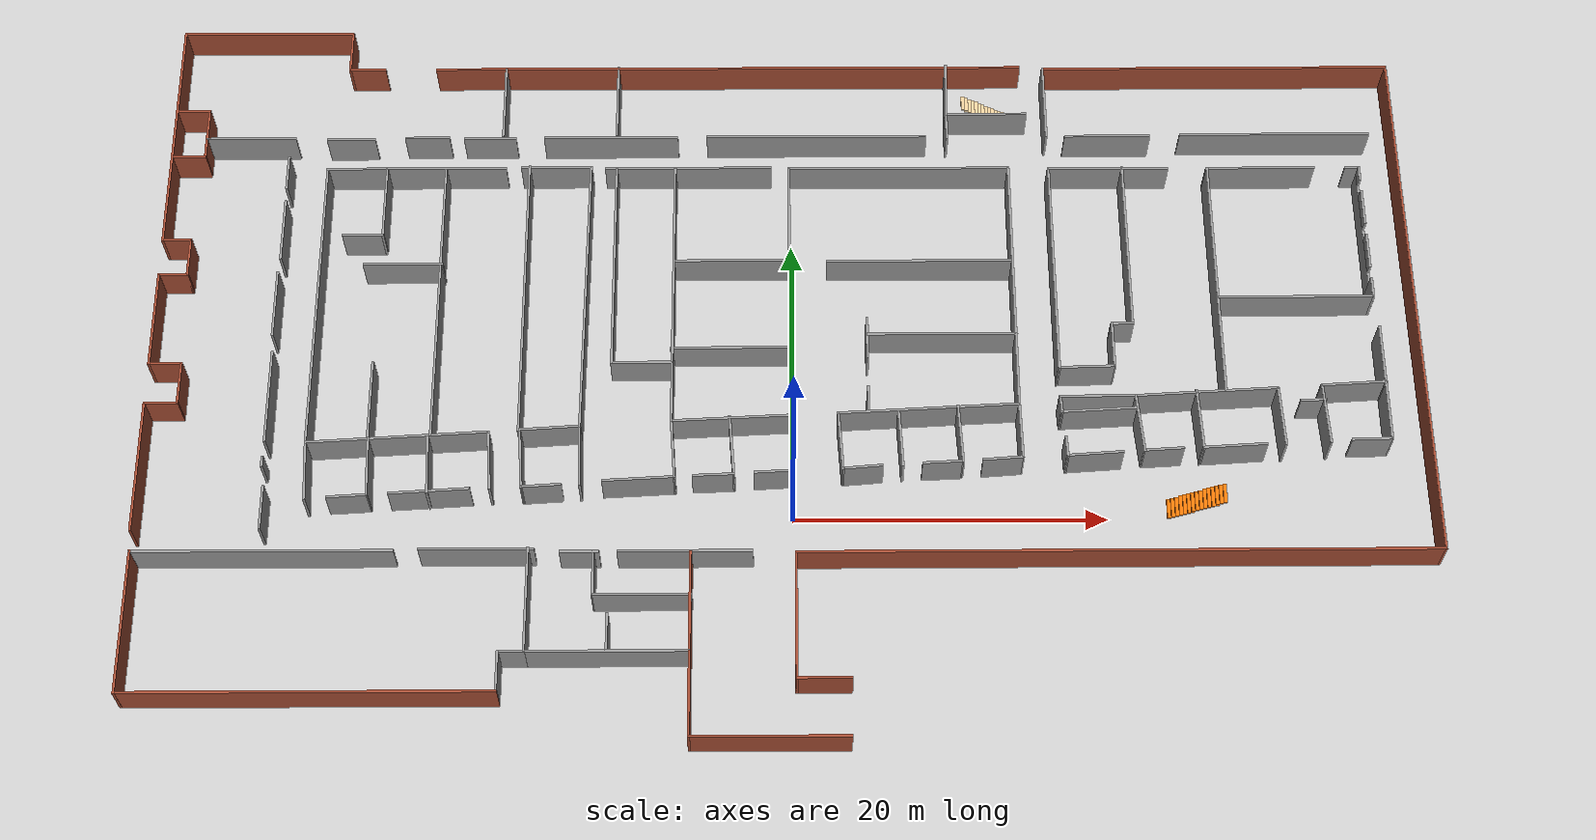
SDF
<sdf version="1.7">
 <world name="default">
  <light name="sun" type="directional">
   <pose>0 0 10 0 -0 0</pose>
   <diffuse>0.8 0.8 0.8 1</diffuse>
   <specular>0.2 0.2 0.2 1</specular>
   <attenuation>
    <range>1000</range>
    <constant>0.9</constant>
    <linear>0.01</linear>
    <quadratic>0.001</quadratic>
   </attenuation>
   <direction>-0.5 0.1 -0.9</direction>
   <spot><inner_angle>0</inner_angle><outer_angle>0</outer_angle><falloff>0</falloff></spot>
  </light>
  <model name="ground_plane">
   <static>1</static>
   <link name="link">
    <collision name="collision">
     <geometry><plane><normal>0 0 1</normal><size>100 100</size></plane></geometry>
     <surface><friction><ode><mu>100</mu><mu2>50</mu2></ode></friction></surface>
    </collision>
    <visual name="visual">
     <cast_shadows>0</cast_shadows>
     <geometry><plane><normal>0 0 1</normal><size>100 100</size></plane></geometry>
     <material>
      <script><uri>file://media/materials/scripts/gazebo.material</uri><name>Gazebo/Grey</name></script>
     </material>
    </visual>
   </link>
  </model>
  <gravity>0 0 -9.8</gravity>
  <magnetic_field>6e-06 2.3e-05 -4.2e-05</magnetic_field>
  <atmosphere type="adiabatic"/>
  <physics type="ode">
   <max_step_size>0.001</max_step_size>
   <real_time_factor>1</real_time_factor>
   <real_time_update_rate>1000</real_time_update_rate>
  </physics>
  <scene><ambient>0.4 0.4 0.4 1</ambient><background>0.7 0.7 0.7 1</background><shadows>1</shadows></scene>
  <spherical_coordinates>
   <surface_model>EARTH_WGS84</surface_model>
   <latitude_deg>0</latitude_deg>
   <longitude_deg>0</longitude_deg>
   <elevation>0</elevation>
   <heading_deg>0</heading_deg>
  </spherical_coordinates>
  <model name="Sherman_ground">
   <pose>-0.396386 10.2382 0 0 -0 0</pose>
   <link name="Stairs_1">
    <visual name="Stairs_1_Visual_0">
     <pose>24.2922 -9.52404 0.083333 0 -0 1.5708</pose>
     <geometry><box><size>1.306 0.233333 0.166667</size></box></geometry>
     <material>
      <script><uri>file://media/materials/scripts/gazebo.material</uri><name>Gazebo/Grey</name></script>
      <ambient>0.996078 0.47451 0.0196078 1</ambient>
     </material>
     <meta><layer>0</layer></meta>
    </visual>
    <collision name="Stairs_1_Collision_0">
     <geometry><box><size>1.306 0.233333 0.166667</size></box></geometry>
     <pose>24.2922 -9.52404 0.083333 0 -0 1.5708</pose>
    </collision>
    <visual name="Stairs_1_Visual_1">
     <pose>24.5255 -9.52404 0.25 0 -0 1.5708</pose>
     <geometry><box><size>1.306 0.233333 0.166667</size></box></geometry>
     <material>
      <script><uri>file://media/materials/scripts/gazebo.material</uri><name>Gazebo/Grey</name></script>
      <ambient>0.996078 0.47451 0.0196078 1</ambient>
     </material>
     <meta><layer>0</layer></meta>
    </visual>
    <collision name="Stairs_1_Collision_1">
     <geometry><box><size>1.306 0.233333 0.166667</size></box></geometry>
     <pose>24.5255 -9.52404 0.25 0 -0 1.5708</pose>
    </collision>
    <visual name="Stairs_1_Visual_2">
     <pose>24.7589 -9.52404 0.416667 0 -0 1.5708</pose>
     <geometry><box><size>1.306 0.233333 0.166667</size></box></geometry>
     <material>
      <script><uri>file://media/materials/scripts/gazebo.material</uri><name>Gazebo/Grey</name></script>
      <ambient>0.996078 0.47451 0.0196078 1</ambient>
     </material>
     <meta><layer>0</layer></meta>
    </visual>
    <collision name="Stairs_1_Collision_2">
     <geometry><box><size>1.306 0.233333 0.166667</size></box></geometry>
     <pose>24.7589 -9.52404 0.416667 0 -0 1.5708</pose>
    </collision>
    <visual name="Stairs_1_Visual_3">
     <pose>24.9922 -9.52404 0.583333 0 -0 1.5708</pose>
     <geometry><box><size>1.306 0.233333 0.166667</size></box></geometry>
     <material>
      <script><uri>file://media/materials/scripts/gazebo.material</uri><name>Gazebo/Grey</name></script>
      <ambient>0.996078 0.47451 0.0196078 1</ambient>
     </material>
     <meta><layer>0</layer></meta>
    </visual>
    <collision name="Stairs_1_Collision_3">
     <geometry><box><size>1.306 0.233333 0.166667</size></box></geometry>
     <pose>24.9922 -9.52404 0.583333 0 -0 1.5708</pose>
    </collision>
    <visual name="Stairs_1_Visual_4">
     <pose>25.2255 -9.52404 0.75 0 -0 1.5708</pose>
     <geometry><box><size>1.306 0.233333 0.166667</size></box></geometry>
     <material>
      <script><uri>file://media/materials/scripts/gazebo.material</uri><name>Gazebo/Grey</name></script>
      <ambient>0.996078 0.47451 0.0196078 1</ambient>
     </material>
     <meta><layer>0</layer></meta>
    </visual>
    <collision name="Stairs_1_Collision_4">
     <geometry><box><size>1.306 0.233333 0.166667</size></box></geometry>
     <pose>25.2255 -9.52404 0.75 0 -0 1.5708</pose>
    </collision>
    <visual name="Stairs_1_Visual_5">
     <pose>25.4589 -9.52404 0.916667 0 -0 1.5708</pose>
     <geometry><box><size>1.306 0.233333 0.166667</size></box></geometry>
     <material>
      <script><uri>file://media/materials/scripts/gazebo.material</uri><name>Gazebo/Grey</name></script>
      <ambient>0.996078 0.47451 0.0196078 1</ambient>
     </material>
     <meta><layer>0</layer></meta>
    </visual>
    <collision name="Stairs_1_Collision_5">
     <geometry><box><size>1.306 0.233333 0.166667</size></box></geometry>
     <pose>25.4589 -9.52404 0.916667 0 -0 1.5708</pose>
    </collision>
    <visual name="Stairs_1_Visual_6">
     <pose>25.6922 -9.52404 1.08333 0 -0 1.5708</pose>
     <geometry><box><size>1.306 0.233333 0.166667</size></box></geometry>
     <material>
      <script><uri>file://media/materials/scripts/gazebo.material</uri><name>Gazebo/Grey</name></script>
      <ambient>0.996078 0.47451 0.0196078 1</ambient>
     </material>
     <meta><layer>0</layer></meta>
    </visual>
    <collision name="Stairs_1_Collision_6">
     <geometry><box><size>1.306 0.233333 0.166667</size></box></geometry>
     <pose>25.6922 -9.52404 1.08333 0 -0 1.5708</pose>
    </collision>
    <visual name="Stairs_1_Visual_7">
     <pose>25.9255 -9.52404 1.25 0 -0 1.5708</pose>
     <geometry><box><size>1.306 0.233333 0.166667</size></box></geometry>
     <material>
      <script><uri>file://media/materials/scripts/gazebo.material</uri><name>Gazebo/Grey</name></script>
      <ambient>0.996078 0.47451 0.0196078 1</ambient>
     </material>
     <meta><layer>0</layer></meta>
    </visual>
    <collision name="Stairs_1_Collision_7">
     <geometry><box><size>1.306 0.233333 0.166667</size></box></geometry>
     <pose>25.9255 -9.52404 1.25 0 -0 1.5708</pose>
    </collision>
    <visual name="Stairs_1_Visual_8">
     <pose>26.1589 -9.52404 1.41667 0 -0 1.5708</pose>
     <geometry><box><size>1.306 0.233333 0.166667</size></box></geometry>
     <material>
      <script><uri>file://media/materials/scripts/gazebo.material</uri><name>Gazebo/Grey</name></script>
      <ambient>0.996078 0.47451 0.0196078 1</ambient>
     </material>
     <meta><layer>0</layer></meta>
    </visual>
    <collision name="Stairs_1_Collision_8">
     <geometry><box><size>1.306 0.233333 0.166667</size></box></geometry>
     <pose>26.1589 -9.52404 1.41667 0 -0 1.5708</pose>
    </collision>
    <visual name="Stairs_1_Visual_9">
     <pose>26.3922 -9.52404 1.58333 0 -0 1.5708</pose>
     <geometry><box><size>1.306 0.233333 0.166667</size></box></geometry>
     <material>
      <script><uri>file://media/materials/scripts/gazebo.material</uri><name>Gazebo/Grey</name></script>
      <ambient>0.996078 0.47451 0.0196078 1</ambient>
     </material>
     <meta><layer>0</layer></meta>
    </visual>
    <collision name="Stairs_1_Collision_9">
     <geometry><box><size>1.306 0.233333 0.166667</size></box></geometry>
     <pose>26.3922 -9.52404 1.58333 0 -0 1.5708</pose>
    </collision>
    <visual name="Stairs_1_Visual_10">
     <pose>26.6255 -9.52404 1.75 0 -0 1.5708</pose>
     <geometry><box><size>1.306 0.233333 0.166667</size></box></geometry>
     <material>
      <script><uri>file://media/materials/scripts/gazebo.material</uri><name>Gazebo/Grey</name></script>
      <ambient>0.996078 0.47451 0.0196078 1</ambient>
     </material>
     <meta><layer>0</layer></meta>
    </visual>
    <collision name="Stairs_1_Collision_10">
     <geometry><box><size>1.306 0.233333 0.166667</size></box></geometry>
     <pose>26.6255 -9.52404 1.75 0 -0 1.5708</pose>
    </collision>
    <visual name="Stairs_1_Visual_11">
     <pose>26.8589 -9.52404 1.91667 0 -0 1.5708</pose>
     <geometry><box><size>1.306 0.233333 0.166667</size></box></geometry>
     <material>
      <script><uri>file://media/materials/scripts/gazebo.material</uri><name>Gazebo/Grey</name></script>
      <ambient>0.996078 0.47451 0.0196078 1</ambient>
     </material>
     <meta><layer>0</layer></meta>
    </visual>
    <collision name="Stairs_1_Collision_11">
     <geometry><box><size>1.306 0.233333 0.166667</size></box></geometry>
     <pose>26.8589 -9.52404 1.91667 0 -0 1.5708</pose>
    </collision>
    <visual name="Stairs_1_Visual_12">
     <pose>27.0922 -9.52404 2.08333 0 -0 1.5708</pose>
     <geometry><box><size>1.306 0.233333 0.166667</size></box></geometry>
     <material>
      <script><uri>file://media/materials/scripts/gazebo.material</uri><name>Gazebo/Grey</name></script>
      <ambient>0.996078 0.47451 0.0196078 1</ambient>
     </material>
     <meta><layer>0</layer></meta>
    </visual>
    <collision name="Stairs_1_Collision_12">
     <geometry><box><size>1.306 0.233333 0.166667</size></box></geometry>
     <pose>27.0922 -9.52404 2.08333 0 -0 1.5708</pose>
    </collision>
    <visual name="Stairs_1_Visual_13">
     <pose>27.3255 -9.52404 2.25 0 -0 1.5708</pose>
     <geometry><box><size>1.306 0.233333 0.166667</size></box></geometry>
     <material>
      <script><uri>file://media/materials/scripts/gazebo.material</uri><name>Gazebo/Grey</name></script>
      <ambient>0.996078 0.47451 0.0196078 1</ambient>
     </material>
     <meta><layer>0</layer></meta>
    </visual>
    <collision name="Stairs_1_Collision_13">
     <geometry><box><size>1.306 0.233333 0.166667</size></box></geometry>
     <pose>27.3255 -9.52404 2.25 0 -0 1.5708</pose>
    </collision>
    <visual name="Stairs_1_Visual_14">
     <pose>27.5589 -9.52403 2.41667 0 -0 1.5708</pose>
     <geometry><box><size>1.306 0.233333 0.166667</size></box></geometry>
     <material>
      <script><uri>file://media/materials/scripts/gazebo.material</uri><name>Gazebo/Grey</name></script>
      <ambient>0.996078 0.47451 0.0196078 1</ambient>
     </material>
     <meta><layer>0</layer></meta>
    </visual>
    <collision name="Stairs_1_Collision_14">
     <geometry><box><size>1.306 0.233333 0.166667</size></box></geometry>
     <pose>27.5589 -9.52403 2.41667 0 -0 1.5708</pose>
    </collision>
   </link>
   <link name="Stairs_2">
    <visual name="Stairs_2_Visual_0">
     <pose>15.3017 19.6509 0.083333 0 -0 -1.5708</pose>
     <geometry><box><size>1 0.233333 0.166667</size></box></geometry>
     <material>
      <script><uri>file://media/materials/scripts/gazebo.material</uri><name>Gazebo/Grey</name></script>
      <ambient>0.921569 0.807843 0.615686 1</ambient>
     </material>
     <meta><layer>0</layer></meta>
    </visual>
    <collision name="Stairs_2_Collision_0">
     <geometry><box><size>1 0.233333 0.166667</size></box></geometry>
     <pose>15.3017 19.6509 0.083333 0 -0 -1.5708</pose>
    </collision>
    <visual name="Stairs_2_Visual_1">
     <pose>15.0684 19.6509 0.25 0 -0 -1.5708</pose>
     <geometry><box><size>1 0.233333 0.166667</size></box></geometry>
     <material>
      <script><uri>file://media/materials/scripts/gazebo.material</uri><name>Gazebo/Grey</name></script>
      <ambient>0.921569 0.807843 0.615686 1</ambient>
     </material>
     <meta><layer>0</layer></meta>
    </visual>
    <collision name="Stairs_2_Collision_1">
     <geometry><box><size>1 0.233333 0.166667</size></box></geometry>
     <pose>15.0684 19.6509 0.25 0 -0 -1.5708</pose>
    </collision>
    <visual name="Stairs_2_Visual_2">
     <pose>14.835 19.6509 0.416667 0 -0 -1.5708</pose>
     <geometry><box><size>1 0.233333 0.166667</size></box></geometry>
     <material>
      <script><uri>file://media/materials/scripts/gazebo.material</uri><name>Gazebo/Grey</name></script>
      <ambient>0.921569 0.807843 0.615686 1</ambient>
     </material>
     <meta><layer>0</layer></meta>
    </visual>
    <collision name="Stairs_2_Collision_2">
     <geometry><box><size>1 0.233333 0.166667</size></box></geometry>
     <pose>14.835 19.6509 0.416667 0 -0 -1.5708</pose>
    </collision>
    <visual name="Stairs_2_Visual_3">
     <pose>14.6017 19.6509 0.583333 0 -0 -1.5708</pose>
     <geometry><box><size>1 0.233333 0.166667</size></box></geometry>
     <material>
      <script><uri>file://media/materials/scripts/gazebo.material</uri><name>Gazebo/Grey</name></script>
      <ambient>0.921569 0.807843 0.615686 1</ambient>
     </material>
     <meta><layer>0</layer></meta>
    </visual>
    <collision name="Stairs_2_Collision_3">
     <geometry><box><size>1 0.233333 0.166667</size></box></geometry>
     <pose>14.6017 19.6509 0.583333 0 -0 -1.5708</pose>
    </collision>
    <visual name="Stairs_2_Visual_4">
     <pose>14.3684 19.6509 0.75 0 -0 -1.5708</pose>
     <geometry><box><size>1 0.233333 0.166667</size></box></geometry>
     <material>
      <script><uri>file://media/materials/scripts/gazebo.material</uri><name>Gazebo/Grey</name></script>
      <ambient>0.921569 0.807843 0.615686 1</ambient>
     </material>
     <meta><layer>0</layer></meta>
    </visual>
    <collision name="Stairs_2_Collision_4">
     <geometry><box><size>1 0.233333 0.166667</size></box></geometry>
     <pose>14.3684 19.6509 0.75 0 -0 -1.5708</pose>
    </collision>
    <visual name="Stairs_2_Visual_5">
     <pose>14.135 19.6509 0.916667 0 -0 -1.5708</pose>
     <geometry><box><size>1 0.233333 0.166667</size></box></geometry>
     <material>
      <script><uri>file://media/materials/scripts/gazebo.material</uri><name>Gazebo/Grey</name></script>
      <ambient>0.921569 0.807843 0.615686 1</ambient>
     </material>
     <meta><layer>0</layer></meta>
    </visual>
    <collision name="Stairs_2_Collision_5">
     <geometry><box><size>1 0.233333 0.166667</size></box></geometry>
     <pose>14.135 19.6509 0.916667 0 -0 -1.5708</pose>
    </collision>
    <visual name="Stairs_2_Visual_6">
     <pose>13.9017 19.6509 1.08333 0 -0 -1.5708</pose>
     <geometry><box><size>1 0.233333 0.166667</size></box></geometry>
     <material>
      <script><uri>file://media/materials/scripts/gazebo.material</uri><name>Gazebo/Grey</name></script>
      <ambient>0.921569 0.807843 0.615686 1</ambient>
     </material>
     <meta><layer>0</layer></meta>
    </visual>
    <collision name="Stairs_2_Collision_6">
     <geometry><box><size>1 0.233333 0.166667</size></box></geometry>
     <pose>13.9017 19.6509 1.08333 0 -0 -1.5708</pose>
    </collision>
    <visual name="Stairs_2_Visual_7">
     <pose>13.6684 19.6509 1.25 0 -0 -1.5708</pose>
     <geometry><box><size>1 0.233333 0.166667</size></box></geometry>
     <material>
      <script><uri>file://media/materials/scripts/gazebo.material</uri><name>Gazebo/Grey</name></script>
      <ambient>0.921569 0.807843 0.615686 1</ambient>
     </material>
     <meta><layer>0</layer></meta>
    </visual>
    <collision name="Stairs_2_Collision_7">
     <geometry><box><size>1 0.233333 0.166667</size></box></geometry>
     <pose>13.6684 19.6509 1.25 0 -0 -1.5708</pose>
    </collision>
    <visual name="Stairs_2_Visual_8">
     <pose>13.435 19.6509 1.41667 0 -0 -1.5708</pose>
     <geometry><box><size>1 0.233333 0.166667</size></box></geometry>
     <material>
      <script><uri>file://media/materials/scripts/gazebo.material</uri><name>Gazebo/Grey</name></script>
      <ambient>0.921569 0.807843 0.615686 1</ambient>
     </material>
     <meta><layer>0</layer></meta>
    </visual>
    <collision name="Stairs_2_Collision_8">
     <geometry><box><size>1 0.233333 0.166667</size></box></geometry>
     <pose>13.435 19.6509 1.41667 0 -0 -1.5708</pose>
    </collision>
    <visual name="Stairs_2_Visual_9">
     <pose>13.2017 19.6509 1.58333 0 -0 -1.5708</pose>
     <geometry><box><size>1 0.233333 0.166667</size></box></geometry>
     <material>
      <script><uri>file://media/materials/scripts/gazebo.material</uri><name>Gazebo/Grey</name></script>
      <ambient>0.921569 0.807843 0.615686 1</ambient>
     </material>
     <meta><layer>0</layer></meta>
    </visual>
    <collision name="Stairs_2_Collision_9">
     <geometry><box><size>1 0.233333 0.166667</size></box></geometry>
     <pose>13.2017 19.6509 1.58333 0 -0 -1.5708</pose>
    </collision>
    <visual name="Stairs_2_Visual_10">
     <pose>12.9684 19.6509 1.75 0 -0 -1.5708</pose>
     <geometry><box><size>1 0.233333 0.166667</size></box></geometry>
     <material>
      <script><uri>file://media/materials/scripts/gazebo.material</uri><name>Gazebo/Grey</name></script>
      <ambient>0.921569 0.807843 0.615686 1</ambient>
     </material>
     <meta><layer>0</layer></meta>
    </visual>
    <collision name="Stairs_2_Collision_10">
     <geometry><box><size>1 0.233333 0.166667</size></box></geometry>
     <pose>12.9684 19.6509 1.75 0 -0 -1.5708</pose>
    </collision>
    <visual name="Stairs_2_Visual_11">
     <pose>12.735 19.6509 1.91667 0 -0 -1.5708</pose>
     <geometry><box><size>1 0.233333 0.166667</size></box></geometry>
     <material>
      <script><uri>file://media/materials/scripts/gazebo.material</uri><name>Gazebo/Grey</name></script>
      <ambient>0.921569 0.807843 0.615686 1</ambient>
     </material>
     <meta><layer>0</layer></meta>
    </visual>
    <collision name="Stairs_2_Collision_11">
     <geometry><box><size>1 0.233333 0.166667</size></box></geometry>
     <pose>12.735 19.6509 1.91667 0 -0 -1.5708</pose>
    </collision>
    <visual name="Stairs_2_Visual_12">
     <pose>12.5017 19.6509 2.08333 0 -0 -1.5708</pose>
     <geometry><box><size>1 0.233333 0.166667</size></box></geometry>
     <material>
      <script><uri>file://media/materials/scripts/gazebo.material</uri><name>Gazebo/Grey</name></script>
      <ambient>0.921569 0.807843 0.615686 1</ambient>
     </material>
     <meta><layer>0</layer></meta>
    </visual>
    <collision name="Stairs_2_Collision_12">
     <geometry><box><size>1 0.233333 0.166667</size></box></geometry>
     <pose>12.5017 19.6509 2.08333 0 -0 -1.5708</pose>
    </collision>
    <visual name="Stairs_2_Visual_13">
     <pose>12.2684 19.6509 2.25 0 -0 -1.5708</pose>
     <geometry><box><size>1 0.233333 0.166667</size></box></geometry>
     <material>
      <script><uri>file://media/materials/scripts/gazebo.material</uri><name>Gazebo/Grey</name></script>
      <ambient>0.921569 0.807843 0.615686 1</ambient>
     </material>
     <meta><layer>0</layer></meta>
    </visual>
    <collision name="Stairs_2_Collision_13">
     <geometry><box><size>1 0.233333 0.166667</size></box></geometry>
     <pose>12.2684 19.6509 2.25 0 -0 -1.5708</pose>
    </collision>
    <visual name="Stairs_2_Visual_14">
     <pose>12.035 19.6509 2.41667 0 -0 -1.5708</pose>
     <geometry><box><size>1 0.233333 0.166667</size></box></geometry>
     <material>
      <script><uri>file://media/materials/scripts/gazebo.material</uri><name>Gazebo/Grey</name></script>
      <ambient>0.921569 0.807843 0.615686 1</ambient>
     </material>
     <meta><layer>0</layer></meta>
    </visual>
    <collision name="Stairs_2_Collision_14">
     <geometry><box><size>1 0.233333 0.166667</size></box></geometry>
     <pose>12.035 19.6509 2.41667 0 -0 -1.5708</pose>
    </collision>
   </link>
   <link name="Wall_0">
    <collision name="Wall_0_Collision">
     <geometry><box><size>17.75 0.15 2.5</size></box></geometry>
     <pose>0 0 1.25 0 -0 0</pose>
    </collision>
    <visual name="Wall_0_Visual">
     <pose>0 0 1.25 0 -0 0</pose>
     <geometry><box><size>17.75 0.15 2.5</size></box></geometry>
     <material>
      <script><uri>file://media/materials/scripts/gazebo.material</uri><name>Gazebo/Grey</name></script>
      <ambient>1 1 1 1</ambient>
     </material>
     <meta><layer>0</layer></meta>
    </visual>
    <pose>14.8884 5.63839 0 0 -0 -1.5708</pose>
   </link>
   <link name="Wall_10">
    <collision name="Wall_10_Collision">
     <geometry><box><size>16.75 0.15 2.5</size></box></geometry>
     <pose>0 0 1.25 0 -0 0</pose>
    </collision>
    <visual name="Wall_10_Visual">
     <pose>0 0 1.25 0 -0 0</pose>
     <geometry><box><size>16.75 0.15 2.5</size></box></geometry>
     <material>
      <script><uri>file://media/materials/scripts/gazebo.material</uri><name>Gazebo/Grey</name></script>
      <ambient>1 1 1 1</ambient>
     </material>
     <meta><layer>0</layer></meta>
    </visual>
    <pose>28.1802 6.12092 0 0 -0 -1.5708</pose>
   </link>
   <link name="Wall_100">
    <collision name="Wall_100_Collision">
     <geometry><box><size>12 0.15 2.5</size></box></geometry>
     <pose>0 0 1.25 0 -0 0</pose>
    </collision>
    <visual name="Wall_100_Visual">
     <pose>0 0 1.25 0 -0 0</pose>
     <geometry><box><size>12 0.15 2.5</size></box></geometry>
     <material>
      <script><uri>file://media/materials/scripts/gazebo.material</uri><name>Gazebo/Grey</name></script>
      <ambient>1 1 1 1</ambient>
     </material>
     <meta><layer>0</layer></meta>
    </visual>
    <pose>22.4926 8.56716 0 0 -0 -1.5708</pose>
   </link>
   <link name="Wall_101">
    <collision name="Wall_101_Collision">
     <geometry><box><size>1.5 0.15 2.5</size></box></geometry>
     <pose>0 0 1.25 0 -0 0</pose>
    </collision>
    <visual name="Wall_101_Visual">
     <pose>0 0 1.25 0 -0 0</pose>
     <geometry><box><size>1.5 0.15 2.5</size></box></geometry>
     <material>
      <script><uri>file://media/materials/scripts/gazebo.material</uri><name>Gazebo/Grey</name></script>
      <ambient>1 1 1 1</ambient>
     </material>
     <meta><layer>0</layer></meta>
    </visual>
    <pose>21.8176 2.64216 0 0 -0 3.14159</pose>
   </link>
   <link name="Wall_104">
    <collision name="Wall_104_Collision">
     <geometry><box><size>3.25 0.15 2.5</size></box></geometry>
     <pose>0 0 1.25 0 -0 0</pose>
    </collision>
    <visual name="Wall_104_Visual">
     <pose>0 0 1.25 0 -0 0</pose>
     <geometry><box><size>3.25 0.15 2.5</size></box></geometry>
     <material>
      <script><uri>file://media/materials/scripts/gazebo.material</uri><name>Gazebo/Grey</name></script>
      <ambient>1 1 1 1</ambient>
     </material>
     <meta><layer>0</layer></meta>
    </visual>
    <pose>21.1426 1.09216 0 0 -0 -1.5708</pose>
   </link>
   <link name="Wall_105">
    <collision name="Wall_105_Collision">
     <geometry><box><size>3.7132 0.15 2.5</size></box></geometry>
     <pose>0 0 1.25 0 -0 0</pose>
    </collision>
    <visual name="Wall_105_Visual">
     <pose>0 0 1.25 0 -0 0</pose>
     <geometry><box><size>3.7132 0.15 2.5</size></box></geometry>
     <material>
      <script><uri>file://media/materials/scripts/gazebo.material</uri><name>Gazebo/Grey</name></script>
      <ambient>1 1 1 1</ambient>
     </material>
     <meta><layer>0</layer></meta>
    </visual>
    <pose>19.3617 -0.507777 0 0 -0 -3.11356</pose>
   </link>
   <link name="Wall_109">
    <collision name="Wall_109_Collision">
     <geometry><box><size>8.5 0.15 2.5</size></box></geometry>
     <pose>0 0 1.25 0 -0 0</pose>
    </collision>
    <visual name="Wall_109_Visual">
     <pose>0 0 1.25 0 -0 0</pose>
     <geometry><box><size>8.5 0.15 2.5</size></box></geometry>
     <material>
      <script><uri>file://media/materials/scripts/gazebo.material</uri><name>Gazebo/Grey</name></script>
      <ambient>1 1 1 1</ambient>
     </material>
     <meta><layer>0</layer></meta>
    </visual>
    <pose>-6.35702 -13.3085 0 0 -0 3.14159</pose>
   </link>
   <link name="Wall_113">
    <collision name="Wall_113_Collision">
     <geometry><box><size>7.25 0.15 2.5</size></box></geometry>
     <pose>0 0 1.25 0 -0 0</pose>
    </collision>
    <visual name="Wall_113_Visual">
     <pose>0 0 1.25 0 -0 0</pose>
     <geometry><box><size>7.25 0.15 2.5</size></box></geometry>
     <material>
      <script><uri>file://media/materials/scripts/gazebo.material</uri><name>Gazebo/Grey</name></script>
      <ambient>1 1 1 1</ambient>
     </material>
     <meta><layer>0</layer></meta>
    </visual>
    <pose>-19.366 -13.1466 0 0 -0 3.14159</pose>
   </link>
   <link name="Wall_117">
    <collision name="Wall_117_Collision">
     <geometry><box><size>4.1198 0.15 2.5</size></box></geometry>
     <pose>0 0 1.25 0 -0 0</pose>
    </collision>
    <visual name="Wall_117_Visual">
     <pose>0 0 1.25 0 -0 0</pose>
     <geometry><box><size>4.1198 0.15 2.5</size></box></geometry>
     <material>
      <script><uri>file://media/materials/scripts/gazebo.material</uri><name>Gazebo/Grey</name></script>
      <ambient>1 1 1 1</ambient>
     </material>
     <meta><layer>0</layer></meta>
    </visual>
    <pose>-30.4407 -7.68509 0 0 -0 -1.51982</pose>
   </link>
   <link name="Wall_119">
    <collision name="Wall_119_Collision">
     <geometry><box><size>11.7407 0.15 2.5</size></box></geometry>
     <pose>0 0 1.25 0 -0 0</pose>
    </collision>
    <visual name="Wall_119_Visual">
     <pose>0 0 1.25 0 -0 0</pose>
     <geometry><box><size>11.7407 0.15 2.5</size></box></geometry>
     <material>
      <script><uri>file://media/materials/scripts/gazebo.material</uri><name>Gazebo/Grey</name></script>
      <ambient>1 1 1 1</ambient>
     </material>
     <meta><layer>0</layer></meta>
    </visual>
    <pose>-24.7567 -5.35889 0 0 -0 0.059371</pose>
   </link>
   <link name="Wall_12">
    <collision name="Wall_12_Collision">
     <geometry><box><size>10.25 0.15 2.5</size></box></geometry>
     <pose>0 0 1.25 0 -0 0</pose>
    </collision>
    <visual name="Wall_12_Visual">
     <pose>0 0 1.25 0 -0 0</pose>
     <geometry><box><size>10.25 0.15 2.5</size></box></geometry>
     <material>
      <script><uri>file://media/materials/scripts/gazebo.material</uri><name>Gazebo/Grey</name></script>
      <ambient>1 1 1 1</ambient>
     </material>
     <meta><layer>0</layer></meta>
    </visual>
    <pose>33.2707 4.59021 0 0 -0 0</pose>
   </link>
   <link name="Wall_120">
    <collision name="Wall_120_Collision">
     <geometry><box><size>4.08169 0.15 2.5</size></box></geometry>
     <pose>0 0 1.25 0 -0 0</pose>
    </collision>
    <visual name="Wall_120_Visual">
     <pose>0 0 1.25 0 -0 0</pose>
     <geometry><box><size>4.08169 0.15 2.5</size></box></geometry>
     <material>
      <script><uri>file://media/materials/scripts/gazebo.material</uri><name>Gazebo/Grey</name></script>
      <ambient>1 1 1 1</ambient>
     </material>
     <meta><layer>0</layer></meta>
    </visual>
    <pose>-18.8502 -6.97712 0 0 -0 -1.50902</pose>
   </link>
   <link name="Wall_122">
    <collision name="Wall_122_Collision">
     <geometry><box><size>4.15837 0.15 2.5</size></box></geometry>
     <pose>0 0 1.25 0 -0 0</pose>
    </collision>
    <visual name="Wall_122_Visual">
     <pose>0 0 1.25 0 -0 0</pose>
     <geometry><box><size>4.15837 0.15 2.5</size></box></geometry>
     <material>
      <script><uri>file://media/materials/scripts/gazebo.material</uri><name>Gazebo/Grey</name></script>
      <ambient>1 1 1 1</ambient>
     </material>
     <meta><layer>0</layer></meta>
    </visual>
    <pose>-22.7339 -7.21985 0 0 -0 -1.53041</pose>
   </link>
   <link name="Wall_124">
    <collision name="Wall_124_Collision">
     <geometry><box><size>5.17612 0.15 2.5</size></box></geometry>
     <pose>0 0 1.25 0 -0 0</pose>
    </collision>
    <visual name="Wall_124_Visual">
     <pose>0 0 1.25 0 -0 0</pose>
     <geometry><box><size>5.17612 0.15 2.5</size></box></geometry>
     <material>
      <script><uri>file://media/materials/scripts/gazebo.material</uri><name>Gazebo/Grey</name></script>
      <ambient>1 1 1 1</ambient>
     </material>
     <meta><layer>0</layer></meta>
    </visual>
    <pose>-22.5272 -9.13677 0 0 -0 0.0609</pose>
   </link>
   <link name="Wall_126">
    <collision name="Wall_126_Collision">
     <geometry><box><size>4.0991 0.15 2.5</size></box></geometry>
     <pose>0 0 1.25 0 -0 0</pose>
    </collision>
    <visual name="Wall_126_Visual">
     <pose>0 0 1.25 0 -0 0</pose>
     <geometry><box><size>4.0991 0.15 2.5</size></box></geometry>
     <material>
      <script><uri>file://media/materials/scripts/gazebo.material</uri><name>Gazebo/Grey</name></script>
      <ambient>1 1 1 1</ambient>
     </material>
     <meta><layer>0</layer></meta>
    </visual>
    <pose>-26.5192 -7.40842 0 0 -0 -1.53206</pose>
   </link>
   <link name="Wall_128">
    <collision name="Wall_128_Collision">
     <geometry><box><size>2.63252 0.15 2.5</size></box></geometry>
     <pose>0 0 1.25 0 -0 0</pose>
    </collision>
    <visual name="Wall_128_Visual">
     <pose>0 0 1.25 0 -0 0</pose>
     <geometry><box><size>2.63252 0.15 2.5</size></box></geometry>
     <material>
      <script><uri>file://media/materials/scripts/gazebo.material</uri><name>Gazebo/Grey</name></script>
      <ambient>1 1 1 1</ambient>
     </material>
     <meta><layer>0</layer></meta>
    </visual>
    <pose>-27.6816 -9.45797 0 0 -0 0.06165</pose>
   </link>
   <link name="Wall_13">
    <pose>38.3207 9.51521 0 0 -0 1.5708</pose>
    <visual name="Wall_13_Visual_0">
     <pose>-4.27248 0 1.25 0 -0 0</pose>
     <geometry><box><size>1.45504 0.15 2.5</size></box></geometry>
     <material>
      <script><uri>file://media/materials/scripts/gazebo.material</uri><name>Gazebo/Grey</name></script>
      <ambient>1 1 1 1</ambient>
     </material>
     <meta><layer>0</layer></meta>
    </visual>
    <collision name="Wall_13_Collision_0">
     <geometry><box><size>1.45504 0.15 2.5</size></box></geometry>
     <pose>-4.27248 0 1.25 0 -0 0</pose>
    </collision>
    <visual name="Wall_13_Visual_1">
     <pose>0.727523 0 0.85 0 -0 0</pose>
     <geometry><box><size>8.54495 0.15 1.7</size></box></geometry>
     <material>
      <script><uri>file://media/materials/scripts/gazebo.material</uri><name>Gazebo/Grey</name></script>
      <ambient>1 1 1 1</ambient>
     </material>
     <meta><layer>0</layer></meta>
    </visual>
    <collision name="Wall_13_Collision_1">
     <geometry><box><size>8.54495 0.15 1.7</size></box></geometry>
     <pose>0.727523 0 0.85 0 -0 0</pose>
    </collision>
    <visual name="Wall_13_Visual_2">
     <pose>-1.5065 0 2.1 0 -0 0</pose>
     <geometry><box><size>2.4769 0.15 0.8</size></box></geometry>
     <material>
      <script><uri>file://media/materials/scripts/gazebo.material</uri><name>Gazebo/Grey</name></script>
      <ambient>1 1 1 1</ambient>
     </material>
     <meta><layer>0</layer></meta>
    </visual>
    <collision name="Wall_13_Collision_2">
     <geometry><box><size>2.4769 0.15 0.8</size></box></geometry>
     <pose>-1.5065 0 2.1 0 -0 0</pose>
    </collision>
    <visual name="Wall_13_Visual_3">
     <pose>1.83108 0 2.1 0 -0 0</pose>
     <geometry><box><size>2.59827 0.15 0.8</size></box></geometry>
     <material>
      <script><uri>file://media/materials/scripts/gazebo.material</uri><name>Gazebo/Grey</name></script>
      <ambient>1 1 1 1</ambient>
     </material>
     <meta><layer>0</layer></meta>
    </visual>
    <collision name="Wall_13_Collision_3">
     <geometry><box><size>2.59827 0.15 0.8</size></box></geometry>
     <pose>1.83108 0 2.1 0 -0 0</pose>
    </collision>
    <visual name="Wall_13_Visual_4">
     <pose>4.46511 0 2.1 0 -0 0</pose>
     <geometry><box><size>1.06978 0.15 0.8</size></box></geometry>
     <material>
      <script><uri>file://media/materials/scripts/gazebo.material</uri><name>Gazebo/Grey</name></script>
      <ambient>1 1 1 1</ambient>
     </material>
     <meta><layer>0</layer></meta>
    </visual>
    <collision name="Wall_13_Collision_4">
     <geometry><box><size>1.06978 0.15 0.8</size></box></geometry>
     <pose>4.46511 0 2.1 0 -0 0</pose>
    </collision>
   </link>
   <link name="Wall_130">
    <collision name="Wall_130_Collision">
     <geometry><box><size>4.66154 0.15 2.5</size></box></geometry>
     <pose>0 0 1.25 0 -0 0</pose>
    </collision>
    <visual name="Wall_130_Visual">
     <pose>0 0 1.25 0 -0 0</pose>
     <geometry><box><size>4.66154 0.15 2.5</size></box></geometry>
     <material>
      <script><uri>file://media/materials/scripts/gazebo.material</uri><name>Gazebo/Grey</name></script>
      <ambient>1 1 1 1</ambient>
     </material>
     <meta><layer>0</layer></meta>
    </visual>
    <pose>-9.35411 -8.3398 0 0 -0 0.054991</pose>
   </link>
   <link name="Wall_132">
    <collision name="Wall_132_Collision">
     <geometry><box><size>4.16245 0.15 2.5</size></box></geometry>
     <pose>0 0 1.25 0 -0 0</pose>
    </collision>
    <visual name="Wall_132_Visual">
     <pose>0 0 1.25 0 -0 0</pose>
     <geometry><box><size>4.16245 0.15 2.5</size></box></geometry>
     <material>
      <script><uri>file://media/materials/scripts/gazebo.material</uri><name>Gazebo/Grey</name></script>
      <ambient>1 1 1 1</ambient>
     </material>
     <meta><layer>0</layer></meta>
    </visual>
    <pose>-16.8571 -6.87607 0 0 -0 -1.51026</pose>
   </link>
   <link name="Wall_133">
    <collision name="Wall_133_Collision">
     <geometry><box><size>2.62309 0.15 2.5</size></box></geometry>
     <pose>0 0 1.25 0 -0 0</pose>
    </collision>
    <visual name="Wall_133_Visual">
     <pose>0 0 1.25 0 -0 0</pose>
     <geometry><box><size>2.62309 0.15 2.5</size></box></geometry>
     <material>
      <script><uri>file://media/materials/scripts/gazebo.material</uri><name>Gazebo/Grey</name></script>
      <ambient>1 1 1 1</ambient>
     </material>
     <meta><layer>0</layer></meta>
    </visual>
    <pose>-15.5018 -8.79771 0 0 -0 0.06548</pose>
   </link>
   <link name="Wall_135">
    <collision name="Wall_135_Collision">
     <geometry><box><size>3.96056 0.15 2.5</size></box></geometry>
     <pose>0 0 1.25 0 -0 0</pose>
    </collision>
    <visual name="Wall_135_Visual">
     <pose>0 0 1.25 0 -0 0</pose>
     <geometry><box><size>3.96056 0.15 2.5</size></box></geometry>
     <material>
      <script><uri>file://media/materials/scripts/gazebo.material</uri><name>Gazebo/Grey</name></script>
      <ambient>1 1 1 1</ambient>
     </material>
     <meta><layer>0</layer></meta>
    </visual>
    <pose>-15.077 -4.75215 0 0 -0 0.063743</pose>
   </link>
   <link name="Wall_136">
    <collision name="Wall_136_Collision">
     <geometry><box><size>4.23782 0.15 2.5</size></box></geometry>
     <pose>0 0 1.25 0 -0 0</pose>
    </collision>
    <visual name="Wall_136_Visual">
     <pose>0 0 1.25 0 -0 0</pose>
     <geometry><box><size>4.23782 0.15 2.5</size></box></geometry>
     <material>
      <script><uri>file://media/materials/scripts/gazebo.material</uri><name>Gazebo/Grey</name></script>
      <ambient>1 1 1 1</ambient>
     </material>
     <meta><layer>0</layer></meta>
    </visual>
    <pose>-13.1149 -6.67379 0 0 -0 -1.5411</pose>
   </link>
   <link name="Wall_138">
    <collision name="Wall_138_Collision">
     <geometry><box><size>19.4165 0.15 2.5</size></box></geometry>
     <pose>0 0 1.25 0 -0 0</pose>
    </collision>
    <visual name="Wall_138_Visual">
     <pose>0 0 1.25 0 -0 0</pose>
     <geometry><box><size>19.4165 0.15 2.5</size></box></geometry>
     <material>
      <script><uri>file://media/materials/scripts/gazebo.material</uri><name>Gazebo/Grey</name></script>
      <ambient>1 1 1 1</ambient>
     </material>
     <meta><layer>0</layer></meta>
    </visual>
    <pose>-13.0667 5.00187 0 0 -0 -1.5821</pose>
   </link>
   <link name="Wall_14">
    <collision name="Wall_14_Collision">
     <geometry><box><size>1 0.15 2.5</size></box></geometry>
     <pose>0 0 1.25 0 -0 0</pose>
    </collision>
    <visual name="Wall_14_Visual">
     <pose>0 0 1.25 0 -0 0</pose>
     <geometry><box><size>1 0.15 2.5</size></box></geometry>
     <material>
      <script><uri>file://media/materials/scripts/gazebo.material</uri><name>Gazebo/Grey</name></script>
      <ambient>1 1 1 1</ambient>
     </material>
     <meta><layer>0</layer></meta>
    </visual>
    <pose>37.8957 14.4402 0 0 -0 3.14159</pose>
   </link>
   <link name="Wall_140">
    <collision name="Wall_140_Collision">
     <geometry><box><size>19.75 0.15 2.5</size></box></geometry>
     <pose>0 0 1.25 0 -0 0</pose>
    </collision>
    <visual name="Wall_140_Visual">
     <pose>0 0 1.25 0 -0 0</pose>
     <geometry><box><size>19.75 0.15 2.5</size></box></geometry>
     <material>
      <script><uri>file://media/materials/scripts/gazebo.material</uri><name>Gazebo/Grey</name></script>
      <ambient>1 1 1 1</ambient>
     </material>
     <meta><layer>0</layer></meta>
    </visual>
    <pose>-17.0706 4.92221 0 0 -0 -1.5708</pose>
   </link>
   <link name="Wall_142">
    <collision name="Wall_142_Collision">
     <geometry><box><size>14.75 0.15 2.5</size></box></geometry>
     <pose>0 0 1.25 0 -0 0</pose>
    </collision>
    <visual name="Wall_142_Visual">
     <pose>0 0 1.25 0 -0 0</pose>
     <geometry><box><size>14.75 0.15 2.5</size></box></geometry>
     <material>
      <script><uri>file://media/materials/scripts/gazebo.material</uri><name>Gazebo/Grey</name></script>
      <ambient>1 1 1 1</ambient>
     </material>
     <meta><layer>0</layer></meta>
    </visual>
    <pose>-11.252 7.23883 0 0 -0 -1.5708</pose>
   </link>
   <link name="Wall_143">
    <collision name="Wall_143_Collision">
     <geometry><box><size>4 0.15 2.5</size></box></geometry>
     <pose>0 0 1.25 0 -0 0</pose>
    </collision>
    <visual name="Wall_143_Visual">
     <pose>0 0 1.25 0 -0 0</pose>
     <geometry><box><size>4 0.15 2.5</size></box></geometry>
     <material>
      <script><uri>file://media/materials/scripts/gazebo.material</uri><name>Gazebo/Grey</name></script>
      <ambient>1 1 1 1</ambient>
     </material>
     <meta><layer>0</layer></meta>
    </visual>
    <pose>-9.32701 -0.061173 0 0 -0 0</pose>
   </link>
   <link name="Wall_145">
    <collision name="Wall_145_Collision">
     <geometry><box><size>20.25 0.15 2.5</size></box></geometry>
     <pose>0 0 1.25 0 -0 0</pose>
    </collision>
    <visual name="Wall_145_Visual">
     <pose>0 0 1.25 0 -0 0</pose>
     <geometry><box><size>20.25 0.15 2.5</size></box></geometry>
     <material>
      <script><uri>file://media/materials/scripts/gazebo.material</uri><name>Gazebo/Grey</name></script>
      <ambient>1 1 1 1</ambient>
     </material>
     <meta><layer>0</layer></meta>
    </visual>
    <pose>-30.5472 4.55394 0 0 -0 -1.5708</pose>
   </link>
   <link name="Wall_147">
    <collision name="Wall_147_Collision">
     <geometry><box><size>5.75 0.15 2.5</size></box></geometry>
     <pose>0 0 1.25 0 -0 0</pose>
    </collision>
    <visual name="Wall_147_Visual">
     <pose>0 0 1.25 0 -0 0</pose>
     <geometry><box><size>5.75 0.15 2.5</size></box></geometry>
     <material>
      <script><uri>file://media/materials/scripts/gazebo.material</uri><name>Gazebo/Grey</name></script>
      <ambient>1 1 1 1</ambient>
     </material>
     <meta><layer>0</layer></meta>
    </visual>
    <pose>-26.6251 -2.78473 0 0 -0 -1.5708</pose>
   </link>
   <link name="Wall_149">
    <collision name="Wall_149_Collision">
     <geometry><box><size>20 0.15 2.5</size></box></geometry>
     <pose>0 0 1.25 0 -0 0</pose>
    </collision>
    <visual name="Wall_149_Visual">
     <pose>0 0 1.25 0 -0 0</pose>
     <geometry><box><size>20 0.15 2.5</size></box></geometry>
     <material>
      <script><uri>file://media/materials/scripts/gazebo.material</uri><name>Gazebo/Grey</name></script>
      <ambient>1 1 1 1</ambient>
     </material>
     <meta><layer>0</layer></meta>
    </visual>
    <pose>-22.6384 4.70426 0 0 -0 -1.5708</pose>
   </link>
   <link name="Wall_151">
    <collision name="Wall_151_Collision">
     <geometry><box><size>5.25 0.15 2.5</size></box></geometry>
     <pose>0 0 1.25 0 -0 0</pose>
    </collision>
    <visual name="Wall_151_Visual">
     <pose>0 0 1.25 0 -0 0</pose>
     <geometry><box><size>5.25 0.15 2.5</size></box></geometry>
     <material>
      <script><uri>file://media/materials/scripts/gazebo.material</uri><name>Gazebo/Grey</name></script>
      <ambient>1 1 1 1</ambient>
     </material>
     <meta><layer>0</layer></meta>
    </visual>
    <pose>-25.1129 7.27848 0 0 -0 0</pose>
   </link>
   <link name="Wall_154">
    <collision name="Wall_154_Collision">
     <geometry><box><size>3 0.15 2.5</size></box></geometry>
     <pose>0 0 1.25 0 -0 0</pose>
    </collision>
    <visual name="Wall_154_Visual">
     <pose>0 0 1.25 0 -0 0</pose>
     <geometry><box><size>3 0.15 2.5</size></box></geometry>
     <material>
      <script><uri>file://media/materials/scripts/gazebo.material</uri><name>Gazebo/Grey</name></script>
      <ambient>1 1 1 1</ambient>
     </material>
     <meta><layer>0</layer></meta>
    </visual>
    <pose>-32.9828 -10.229 0 0 -0 1.5708</pose>
   </link>
   <link name="Wall_156">
    <collision name="Wall_156_Collision">
     <geometry><box><size>0.75 0.15 2.5</size></box></geometry>
     <pose>0 0 1.25 0 -0 0</pose>
    </collision>
    <visual name="Wall_156_Visual">
     <pose>0 0 1.25 0 -0 0</pose>
     <geometry><box><size>0.75 0.15 2.5</size></box></geometry>
     <material>
      <script><uri>file://media/materials/scripts/gazebo.material</uri><name>Gazebo/Grey</name></script>
      <ambient>1 1 1 1</ambient>
     </material>
     <meta><layer>0</layer></meta>
    </visual>
    <pose>-33.1938 -7.02705 0 0 -0 1.5708</pose>
   </link>
   <link name="Wall_158">
    <collision name="Wall_158_Collision">
     <geometry><box><size>6.5 0.15 2.5</size></box></geometry>
     <pose>0 0 1.25 0 -0 0</pose>
    </collision>
    <visual name="Wall_158_Visual">
     <pose>0 0 1.25 0 -0 0</pose>
     <geometry><box><size>6.5 0.15 2.5</size></box></geometry>
     <material>
      <script><uri>file://media/materials/scripts/gazebo.material</uri><name>Gazebo/Grey</name></script>
      <ambient>1 1 1 1</ambient>
     </material>
     <meta><layer>0</layer></meta>
    </visual>
    <pose>-33.1587 -2.39312 0 0 -0 1.5708</pose>
   </link>
   <link name="Wall_16">
    <collision name="Wall_16_Collision">
     <geometry><box><size>7.25 0.15 2.5</size></box></geometry>
     <pose>0 0 1.25 0 -0 0</pose>
    </collision>
    <visual name="Wall_16_Visual">
     <pose>0 0 1.25 0 -0 0</pose>
     <geometry><box><size>7.25 0.15 2.5</size></box></geometry>
     <material>
      <script><uri>file://media/materials/scripts/gazebo.material</uri><name>Gazebo/Grey</name></script>
      <ambient>1 1 1 1</ambient>
     </material>
     <meta><layer>0</layer></meta>
    </visual>
    <pose>31.7302 14.4209 0 0 -0 0</pose>
   </link>
   <link name="Wall_160">
    <collision name="Wall_160_Collision">
     <geometry><box><size>4.75 0.15 2.5</size></box></geometry>
     <pose>0 0 1.25 0 -0 0</pose>
    </collision>
    <visual name="Wall_160_Visual">
     <pose>0 0 1.25 0 -0 0</pose>
     <geometry><box><size>4.75 0.15 2.5</size></box></geometry>
     <material>
      <script><uri>file://media/materials/scripts/gazebo.material</uri><name>Gazebo/Grey</name></script>
      <ambient>1 1 1 1</ambient>
     </material>
     <meta><layer>0</layer></meta>
    </visual>
    <pose>-33.2656 4.37213 0 0 -0 1.5708</pose>
   </link>
   <link name="Wall_163">
    <collision name="Wall_163_Collision">
     <geometry><box><size>4.5 0.15 2.5</size></box></geometry>
     <pose>0 0 1.25 0 -0 0</pose>
    </collision>
    <visual name="Wall_163_Visual">
     <pose>0 0 1.25 0 -0 0</pose>
     <geometry><box><size>4.5 0.15 2.5</size></box></geometry>
     <material>
      <script><uri>file://media/materials/scripts/gazebo.material</uri><name>Gazebo/Grey</name></script>
      <ambient>1 1 1 1</ambient>
     </material>
     <meta><layer>0</layer></meta>
    </visual>
    <pose>-33.1739 9.93691 0 0 -0 1.5708</pose>
   </link>
   <link name="Wall_165">
    <collision name="Wall_165_Collision">
     <geometry><box><size>2.5 0.15 2.5</size></box></geometry>
     <pose>0 0 1.25 0 -0 0</pose>
    </collision>
    <visual name="Wall_165_Visual">
     <pose>0 0 1.25 0 -0 0</pose>
     <geometry><box><size>2.5 0.15 2.5</size></box></geometry>
     <material>
      <script><uri>file://media/materials/scripts/gazebo.material</uri><name>Gazebo/Grey</name></script>
      <ambient>1 1 1 1</ambient>
     </material>
     <meta><layer>0</layer></meta>
    </visual>
    <pose>-33.2045 14.3514 0 0 -0 1.5708</pose>
   </link>
   <link name="Wall_167">
    <collision name="Wall_167_Collision">
     <geometry><box><size>3.25 0.15 2.5</size></box></geometry>
     <pose>0 0 1.25 0 -0 0</pose>
    </collision>
    <visual name="Wall_167_Visual">
     <pose>0 0 1.25 0 -0 0</pose>
     <geometry><box><size>3.25 0.15 2.5</size></box></geometry>
     <material>
      <script><uri>file://media/materials/scripts/gazebo.material</uri><name>Gazebo/Grey</name></script>
      <ambient>1 1 1 1</ambient>
     </material>
     <meta><layer>0</layer></meta>
    </visual>
    <pose>-29.148 16.9198 0 0 -0 0</pose>
   </link>
   <link name="Wall_169">
    <collision name="Wall_169_Collision">
     <geometry><box><size>3 0.15 2.5</size></box></geometry>
     <pose>0 0 1.25 0 -0 0</pose>
    </collision>
    <visual name="Wall_169_Visual">
     <pose>0 0 1.25 0 -0 0</pose>
     <geometry><box><size>3 0.15 2.5</size></box></geometry>
     <material>
      <script><uri>file://media/materials/scripts/gazebo.material</uri><name>Gazebo/Grey</name></script>
      <ambient>1 1 1 1</ambient>
     </material>
     <meta><layer>0</layer></meta>
    </visual>
    <pose>-24.0327 17.0262 0 0 -0 0</pose>
   </link>
   <link name="Wall_171">
    <collision name="Wall_171_Collision">
     <geometry><box><size>3.5 0.15 2.5</size></box></geometry>
     <pose>0 0 1.25 0 -0 0</pose>
    </collision>
    <visual name="Wall_171_Visual">
     <pose>0 0 1.25 0 -0 0</pose>
     <geometry><box><size>3.5 0.15 2.5</size></box></geometry>
     <material>
      <script><uri>file://media/materials/scripts/gazebo.material</uri><name>Gazebo/Grey</name></script>
      <ambient>1 1 1 1</ambient>
     </material>
     <meta><layer>0</layer></meta>
    </visual>
    <pose>-19.8193 16.973 0 0 -0 0</pose>
   </link>
   <link name="Wall_173">
    <collision name="Wall_173_Collision">
     <geometry><box><size>9 0.15 2.5</size></box></geometry>
     <pose>0 0 1.25 0 -0 0</pose>
    </collision>
    <visual name="Wall_173_Visual">
     <pose>0 0 1.25 0 -0 0</pose>
     <geometry><box><size>9 0.15 2.5</size></box></geometry>
     <material>
      <script><uri>file://media/materials/scripts/gazebo.material</uri><name>Gazebo/Grey</name></script>
      <ambient>1 1 1 1</ambient>
     </material>
     <meta><layer>0</layer></meta>
    </visual>
    <pose>-11.6961 16.9996 0 0 -0 0</pose>
   </link>
   <link name="Wall_175">
    <collision name="Wall_175_Collision">
     <geometry><box><size>14.75 0.15 2.5</size></box></geometry>
     <pose>0 0 1.25 0 -0 0</pose>
    </collision>
    <visual name="Wall_175_Visual">
     <pose>0 0 1.25 0 -0 0</pose>
     <geometry><box><size>14.75 0.15 2.5</size></box></geometry>
     <material>
      <script><uri>file://media/materials/scripts/gazebo.material</uri><name>Gazebo/Grey</name></script>
      <ambient>1 1 1 1</ambient>
     </material>
     <meta><layer>0</layer></meta>
    </visual>
    <pose>2.11161 17.0262 0 0 -0 0</pose>
   </link>
   <link name="Wall_177">
    <collision name="Wall_177_Collision">
     <geometry><box><size>2 0.15 2.5</size></box></geometry>
     <pose>0 0 1.25 0 -0 0</pose>
    </collision>
    <visual name="Wall_177_Visual">
     <pose>0 0 1.25 0 -0 0</pose>
     <geometry><box><size>2 0.15 2.5</size></box></geometry>
     <material>
      <script><uri>file://media/materials/scripts/gazebo.material</uri><name>Gazebo/Grey</name></script>
      <ambient>1 1 1 1</ambient>
     </material>
     <meta><layer>0</layer></meta>
    </visual>
    <pose>10.88 17.8437 0 0 -0 -1.5708</pose>
   </link>
   <link name="Wall_179">
    <collision name="Wall_179_Collision">
     <geometry><box><size>5.5 0.15 2.5</size></box></geometry>
     <pose>0 0 1.25 0 -0 0</pose>
    </collision>
    <visual name="Wall_179_Visual">
     <pose>0 0 1.25 0 -0 0</pose>
     <geometry><box><size>5.5 0.15 2.5</size></box></geometry>
     <material>
      <script><uri>file://media/materials/scripts/gazebo.material</uri><name>Gazebo/Grey</name></script>
      <ambient>1 1 1 1</ambient>
     </material>
     <meta><layer>0</layer></meta>
    </visual>
    <pose>13.555 18.7687 0 0 -0 0</pose>
   </link>
   <link name="Wall_18">
    <collision name="Wall_18_Collision">
     <geometry><box><size>35.9387 0.15 2.5</size></box></geometry>
     <pose>0 0 1.25 0 -0 0</pose>
    </collision>
    <visual name="Wall_18_Visual">
     <pose>0 0 1.25 0 -0 0</pose>
     <geometry><box><size>35.9387 0.15 2.5</size></box></geometry>
     <material>
      <script><uri>file://media/materials/scripts/gazebo.material</uri><name>Gazebo/Bricks</name></script>
      <ambient>1 1 1 1</ambient>
     </material>
     <meta><layer>0</layer></meta>
    </visual>
    <pose>40.9852 4.53689 0 0 -0 -1.56736</pose>
   </link>
   <link name="Wall_181">
    <collision name="Wall_181_Collision">
     <geometry><box><size>5.5 0.15 2.5</size></box></geometry>
     <pose>0 0 1.25 0 -0 0</pose>
    </collision>
    <visual name="Wall_181_Visual">
     <pose>0 0 1.25 0 -0 0</pose>
     <geometry><box><size>5.5 0.15 2.5</size></box></geometry>
     <material>
      <script><uri>file://media/materials/scripts/gazebo.material</uri><name>Gazebo/Grey</name></script>
      <ambient>1 1 1 1</ambient>
     </material>
     <meta><layer>0</layer></meta>
    </visual>
    <pose>17.5612 19.7122 0 0 -0 1.5708</pose>
   </link>
   <link name="Wall_183">
    <collision name="Wall_183_Collision">
     <geometry><box><size>5.75 0.15 2.5</size></box></geometry>
     <pose>0 0 1.25 0 -0 0</pose>
    </collision>
    <visual name="Wall_183_Visual">
     <pose>0 0 1.25 0 -0 0</pose>
     <geometry><box><size>5.75 0.15 2.5</size></box></geometry>
     <material>
      <script><uri>file://media/materials/scripts/gazebo.material</uri><name>Gazebo/Grey</name></script>
      <ambient>1 1 1 1</ambient>
     </material>
     <meta><layer>0</layer></meta>
    </visual>
    <pose>21.6631 16.9801 0 0 -0 0</pose>
   </link>
   <link name="Wall_185">
    <collision name="Wall_185_Collision">
     <geometry><box><size>12.75 0.15 2.5</size></box></geometry>
     <pose>0 0 1.25 0 -0 0</pose>
    </collision>
    <visual name="Wall_185_Visual">
     <pose>0 0 1.25 0 -0 0</pose>
     <geometry><box><size>12.75 0.15 2.5</size></box></geometry>
     <material>
      <script><uri>file://media/materials/scripts/gazebo.material</uri><name>Gazebo/Grey</name></script>
      <ambient>1 1 1 1</ambient>
     </material>
     <meta><layer>0</layer></meta>
    </visual>
    <pose>32.9068 17.0807 0 0 -0 0</pose>
   </link>
   <link name="Wall_187">
    <collision name="Wall_187_Collision">
     <geometry><box><size>23.5125 0.15 2.5</size></box></geometry>
     <pose>0 0 1.25 0 -0 0</pose>
    </collision>
    <visual name="Wall_187_Visual">
     <pose>0 0 1.25 0 -0 0</pose>
     <geometry><box><size>23.5125 0.15 2.5</size></box></geometry>
     <material>
      <script><uri>file://media/materials/scripts/gazebo.material</uri><name>Gazebo/Bricks</name></script>
      <ambient>1 1 1 1</ambient>
     </material>
     <meta><layer>0</layer></meta>
    </visual>
    <pose>29.2425 22.4092 0 0 -0 0.00188</pose>
   </link>
   <link name="Wall_189">
    <collision name="Wall_189_Collision">
     <geometry><box><size>39.75 0.15 2.5</size></box></geometry>
     <pose>0 0 1.25 0 -0 0</pose>
    </collision>
    <visual name="Wall_189_Visual">
     <pose>0 0 1.25 0 -0 0</pose>
     <geometry><box><size>39.75 0.15 2.5</size></box></geometry>
     <material>
      <script><uri>file://media/materials/scripts/gazebo.material</uri><name>Gazebo/Bricks</name></script>
      <ambient>1 1 1 1</ambient>
     </material>
     <meta><layer>0</layer></meta>
    </visual>
    <pose>-3.85525 22.5181 0 0 -0 0</pose>
   </link>
   <link name="Wall_191">
    <collision name="Wall_191_Collision">
     <geometry><box><size>2.5 0.15 2.5</size></box></geometry>
     <pose>0 0 1.25 0 -0 0</pose>
    </collision>
    <visual name="Wall_191_Visual">
     <pose>0 0 1.25 0 -0 0</pose>
     <geometry><box><size>2.5 0.15 2.5</size></box></geometry>
     <material>
      <script><uri>file://media/materials/scripts/gazebo.material</uri><name>Gazebo/Bricks</name></script>
      <ambient>1 1 1 1</ambient>
     </material>
     <meta><layer>0</layer></meta>
    </visual>
    <pose>-28.4037 22.5247 0 0 -0 0</pose>
   </link>
   <link name="Wall_193">
    <collision name="Wall_193_Collision">
     <geometry><box><size>3.10502 0.15 2.5</size></box></geometry>
     <pose>0 0 1.25 0 -0 0</pose>
    </collision>
    <visual name="Wall_193_Visual">
     <pose>0 0 1.25 0 -0 0</pose>
     <geometry><box><size>3.10502 0.15 2.5</size></box></geometry>
     <material>
      <script><uri>file://media/materials/scripts/gazebo.material</uri><name>Gazebo/Bricks</name></script>
      <ambient>1 1 1 1</ambient>
     </material>
     <meta><layer>0</layer></meta>
    </visual>
    <pose>-29.5787 24.0022 0 0 -0 -1.5708</pose>
   </link>
   <link name="Wall_196">
    <collision name="Wall_196_Collision">
     <geometry><box><size>11.5 0.15 2.5</size></box></geometry>
     <pose>0 0 1.25 0 -0 0</pose>
    </collision>
    <visual name="Wall_196_Visual">
     <pose>0 0 1.25 0 -0 0</pose>
     <geometry><box><size>11.5 0.15 2.5</size></box></geometry>
     <material>
      <script><uri>file://media/materials/scripts/gazebo.material</uri><name>Gazebo/Bricks</name></script>
      <ambient>1 1 1 1</ambient>
     </material>
     <meta><layer>0</layer></meta>
    </visual>
    <pose>-35.2537 25.4797 0 0 -0 3.14159</pose>
   </link>
   <link name="Wall_198">
    <collision name="Wall_198_Collision">
     <geometry><box><size>16.5 0.15 2.5</size></box></geometry>
     <pose>0 0 1.25 0 -0 0</pose>
    </collision>
    <visual name="Wall_198_Visual">
     <pose>0 0 1.25 0 -0 0</pose>
     <geometry><box><size>16.5 0.15 2.5</size></box></geometry>
     <material>
      <script><uri>file://media/materials/scripts/gazebo.material</uri><name>Gazebo/Bricks</name></script>
      <ambient>1 1 1 1</ambient>
     </material>
     <meta><layer>0</layer></meta>
    </visual>
    <pose>-41.047 17.3369 0 0 -0 1.5708</pose>
   </link>
   <link name="Wall_2">
    <collision name="Wall_2_Collision">
     <geometry><box><size>14.75 0.15 2.5</size></box></geometry>
     <pose>0 0 1.25 0 -0 0</pose>
    </collision>
    <visual name="Wall_2_Visual">
     <pose>0 0 1.25 0 -0 0</pose>
     <geometry><box><size>14.75 0.15 2.5</size></box></geometry>
     <material>
      <script><uri>file://media/materials/scripts/gazebo.material</uri><name>Gazebo/Grey</name></script>
      <ambient>1 1 1 1</ambient>
     </material>
     <meta><layer>0</layer></meta>
    </visual>
    <pose>7.53881 14.5026 0 0 -0 0</pose>
   </link>
   <link name="Wall_20">
    <collision name="Wall_20_Collision">
     <geometry><box><size>40.5616 0.15 2.5</size></box></geometry>
     <pose>0 0 1.25 0 -0 0</pose>
    </collision>
    <visual name="Wall_20_Visual">
     <pose>0 0 1.25 0 -0 0</pose>
     <geometry><box><size>40.5616 0.15 2.5</size></box></geometry>
     <material>
      <script><uri>file://media/materials/scripts/gazebo.material</uri><name>Gazebo/Bricks</name></script>
      <ambient>1 1 1 1</ambient>
     </material>
     <meta><layer>0</layer></meta>
    </visual>
    <pose>20.7795 -13.3881 0 0 -0 -3.14007</pose>
   </link>
   <link name="Wall_200">
    <collision name="Wall_200_Collision">
     <geometry><box><size>2.25 0.15 2.5</size></box></geometry>
     <pose>0 0 1.25 0 -0 0</pose>
    </collision>
    <visual name="Wall_200_Visual">
     <pose>0 0 1.25 0 -0 0</pose>
     <geometry><box><size>2.25 0.15 2.5</size></box></geometry>
     <material>
      <script><uri>file://media/materials/scripts/gazebo.material</uri><name>Gazebo/Bricks</name></script>
      <ambient>1 1 1 1</ambient>
     </material>
     <meta><layer>0</layer></meta>
    </visual>
    <pose>-39.8915 19.1827 0 0 -0 0</pose>
   </link>
   <link name="Wall_201">
    <collision name="Wall_201_Collision">
     <geometry><box><size>3.75 0.15 2.5</size></box></geometry>
     <pose>0 0 1.25 0 -0 0</pose>
    </collision>
    <visual name="Wall_201_Visual">
     <pose>0 0 1.25 0 -0 0</pose>
     <geometry><box><size>3.75 0.15 2.5</size></box></geometry>
     <material>
      <script><uri>file://media/materials/scripts/gazebo.material</uri><name>Gazebo/Bricks</name></script>
      <ambient>1 1 1 1</ambient>
     </material>
     <meta><layer>0</layer></meta>
    </visual>
    <pose>-38.8415 17.3827 0 0 -0 -1.5708</pose>
   </link>
   <link name="Wall_202">
    <collision name="Wall_202_Collision">
     <geometry><box><size>2.25 0.15 2.5</size></box></geometry>
     <pose>0 0 1.25 0 -0 0</pose>
    </collision>
    <visual name="Wall_202_Visual">
     <pose>0 0 1.25 0 -0 0</pose>
     <geometry><box><size>2.25 0.15 2.5</size></box></geometry>
     <material>
      <script><uri>file://media/materials/scripts/gazebo.material</uri><name>Gazebo/Bricks</name></script>
      <ambient>1 1 1 1</ambient>
     </material>
     <meta><layer>0</layer></meta>
    </visual>
    <pose>-39.8915 15.5827 0 0 -0 3.14159</pose>
   </link>
   <link name="Wall_205">
    <collision name="Wall_205_Collision">
     <geometry><box><size>6 0.15 2.5</size></box></geometry>
     <pose>0 0 1.25 0 -0 0</pose>
    </collision>
    <visual name="Wall_205_Visual">
     <pose>0 0 1.25 0 -0 0</pose>
     <geometry><box><size>6 0.15 2.5</size></box></geometry>
     <material>
      <script><uri>file://media/materials/scripts/gazebo.material</uri><name>Gazebo/Grey</name></script>
      <ambient>1 1 1 1</ambient>
     </material>
     <meta><layer>0</layer></meta>
    </visual>
    <pose>-35.8547 17.01 0 0 -0 0</pose>
   </link>
   <link name="Wall_207">
    <collision name="Wall_207_Collision">
     <geometry><box><size>5.25 0.15 2.5</size></box></geometry>
     <pose>0 0 1.25 0 -0 0</pose>
    </collision>
    <visual name="Wall_207_Visual">
     <pose>0 0 1.25 0 -0 0</pose>
     <geometry><box><size>5.25 0.15 2.5</size></box></geometry>
     <material>
      <script><uri>file://media/materials/scripts/gazebo.material</uri><name>Gazebo/Grey</name></script>
      <ambient>1 1 1 1</ambient>
     </material>
     <meta><layer>0</layer></meta>
    </visual>
    <pose>-26.5742 12.0433 0 0 -0 -1.5708</pose>
   </link>
   <link name="Wall_208">
    <collision name="Wall_208_Collision">
     <geometry><box><size>2.75 0.15 2.5</size></box></geometry>
     <pose>0 0 1.25 0 -0 0</pose>
    </collision>
    <visual name="Wall_208_Visual">
     <pose>0 0 1.25 0 -0 0</pose>
     <geometry><box><size>2.75 0.15 2.5</size></box></geometry>
     <material>
      <script><uri>file://media/materials/scripts/gazebo.material</uri><name>Gazebo/Grey</name></script>
      <ambient>1 1 1 1</ambient>
     </material>
     <meta><layer>0</layer></meta>
    </visual>
    <pose>-27.8742 9.49334 0 0 -0 3.14159</pose>
   </link>
   <link name="Wall_210">
    <collision name="Wall_210_Collision">
     <geometry><box><size>2 0.15 2.5</size></box></geometry>
     <pose>0 0 1.25 0 -0 0</pose>
    </collision>
    <visual name="Wall_210_Visual">
     <pose>0 0 1.25 0 -0 0</pose>
     <geometry><box><size>2 0.15 2.5</size></box></geometry>
     <material>
      <script><uri>file://media/materials/scripts/gazebo.material</uri><name>Gazebo/Bricks</name></script>
      <ambient>1 1 1 1</ambient>
     </material>
     <meta><layer>0</layer></meta>
    </visual>
    <pose>-40.122 9.16193 0 0 -0 0</pose>
   </link>
   <link name="Wall_211">
    <collision name="Wall_211_Collision">
     <geometry><box><size>2.75 0.15 2.5</size></box></geometry>
     <pose>0 0 1.25 0 -0 0</pose>
    </collision>
    <visual name="Wall_211_Visual">
     <pose>0 0 1.25 0 -0 0</pose>
     <geometry><box><size>2.75 0.15 2.5</size></box></geometry>
     <material>
      <script><uri>file://media/materials/scripts/gazebo.material</uri><name>Gazebo/Bricks</name></script>
      <ambient>1 1 1 1</ambient>
     </material>
     <meta><layer>0</layer></meta>
    </visual>
    <pose>-39.197 7.86194 0 0 -0 -1.5708</pose>
   </link>
   <link name="Wall_212">
    <collision name="Wall_212_Collision">
     <geometry><box><size>2 0.15 2.5</size></box></geometry>
     <pose>0 0 1.25 0 -0 0</pose>
    </collision>
    <visual name="Wall_212_Visual">
     <pose>0 0 1.25 0 -0 0</pose>
     <geometry><box><size>2 0.15 2.5</size></box></geometry>
     <material>
      <script><uri>file://media/materials/scripts/gazebo.material</uri><name>Gazebo/Bricks</name></script>
      <ambient>1 1 1 1</ambient>
     </material>
     <meta><layer>0</layer></meta>
    </visual>
    <pose>-40.122 6.56194 0 0 -0 3.14159</pose>
   </link>
   <link name="Wall_213">
    <collision name="Wall_213_Collision">
     <geometry><box><size>6.75 0.15 2.5</size></box></geometry>
     <pose>0 0 1.25 0 -0 0</pose>
    </collision>
    <visual name="Wall_213_Visual">
     <pose>0 0 1.25 0 -0 0</pose>
     <geometry><box><size>6.75 0.15 2.5</size></box></geometry>
     <material>
      <script><uri>file://media/materials/scripts/gazebo.material</uri><name>Gazebo/Bricks</name></script>
      <ambient>1 1 1 1</ambient>
     </material>
     <meta><layer>0</layer></meta>
    </visual>
    <pose>-41.047 3.26193 0 0 -0 -1.5708</pose>
   </link>
   <link name="Wall_214">
    <collision name="Wall_214_Collision">
     <geometry><box><size>2.25 0.15 2.5</size></box></geometry>
     <pose>0 0 1.25 0 -0 0</pose>
    </collision>
    <visual name="Wall_214_Visual">
     <pose>0 0 1.25 0 -0 0</pose>
     <geometry><box><size>2.25 0.15 2.5</size></box></geometry>
     <material>
      <script><uri>file://media/materials/scripts/gazebo.material</uri><name>Gazebo/Bricks</name></script>
      <ambient>1 1 1 1</ambient>
     </material>
     <meta><layer>0</layer></meta>
    </visual>
    <pose>-39.997 -0.038065 0 0 -0 0</pose>
   </link>
   <link name="Wall_215">
    <collision name="Wall_215_Collision">
     <geometry><box><size>3 0.15 2.5</size></box></geometry>
     <pose>0 0 1.25 0 -0 0</pose>
    </collision>
    <visual name="Wall_215_Visual">
     <pose>0 0 1.25 0 -0 0</pose>
     <geometry><box><size>3 0.15 2.5</size></box></geometry>
     <material>
      <script><uri>file://media/materials/scripts/gazebo.material</uri><name>Gazebo/Bricks</name></script>
      <ambient>1 1 1 1</ambient>
     </material>
     <meta><layer>0</layer></meta>
    </visual>
    <pose>-38.947 -1.46307 0 0 -0 -1.5708</pose>
   </link>
   <link name="Wall_216">
    <collision name="Wall_216_Collision">
     <geometry><box><size>2.25 0.15 2.5</size></box></geometry>
     <pose>0 0 1.25 0 -0 0</pose>
    </collision>
    <visual name="Wall_216_Visual">
     <pose>0 0 1.25 0 -0 0</pose>
     <geometry><box><size>2.25 0.15 2.5</size></box></geometry>
     <material>
      <script><uri>file://media/materials/scripts/gazebo.material</uri><name>Gazebo/Bricks</name></script>
      <ambient>1 1 1 1</ambient>
     </material>
     <meta><layer>0</layer></meta>
    </visual>
    <pose>-39.997 -2.88807 0 0 -0 3.14159</pose>
   </link>
   <link name="Wall_218">
    <collision name="Wall_218_Collision">
     <geometry><box><size>9 0.15 2.5</size></box></geometry>
     <pose>0 0 1.25 0 -0 0</pose>
    </collision>
    <visual name="Wall_218_Visual">
     <pose>0 0 1.25 0 -0 0</pose>
     <geometry><box><size>9 0.15 2.5</size></box></geometry>
     <material>
      <script><uri>file://media/materials/scripts/gazebo.material</uri><name>Gazebo/Bricks</name></script>
      <ambient>1 1 1 1</ambient>
     </material>
     <meta><layer>0</layer></meta>
    </visual>
    <pose>-41.047 -7.31306 0 0 -0 -1.5708</pose>
   </link>
   <link name="Wall_22">
    <collision name="Wall_22_Collision">
     <geometry><box><size>4.25 0.15 2.5</size></box></geometry>
     <pose>0 0 1.25 0 -0 0</pose>
    </collision>
    <visual name="Wall_22_Visual">
     <pose>0 0 1.25 0 -0 0</pose>
     <geometry><box><size>4.25 0.15 2.5</size></box></geometry>
     <material>
      <script><uri>file://media/materials/scripts/gazebo.material</uri><name>Gazebo/Grey</name></script>
      <ambient>1 1 1 1</ambient>
     </material>
     <meta><layer>0</layer></meta>
    </visual>
    <pose>38.4787 0.237689 0 0 -0 -1.5708</pose>
   </link>
   <link name="Wall_221">
    <collision name="Wall_221_Collision">
     <geometry><box><size>8.5 0.15 2.5</size></box></geometry>
     <pose>0 0 1.25 0 -0 0</pose>
    </collision>
    <visual name="Wall_221_Visual">
     <pose>0 0 1.25 0 -0 0</pose>
     <geometry><box><size>8.5 0.15 2.5</size></box></geometry>
     <material>
      <script><uri>file://media/materials/scripts/gazebo.material</uri><name>Gazebo/Bricks</name></script>
      <ambient>1 1 1 1</ambient>
     </material>
     <meta><layer>0</layer></meta>
    </visual>
    <pose>0.573709 -17.5939 0 0 -0 -1.5708</pose>
   </link>
   <link name="Wall_222">
    <collision name="Wall_222_Collision">
     <geometry><box><size>3.5 0.15 2.5</size></box></geometry>
     <pose>0 0 1.25 0 -0 0</pose>
    </collision>
    <visual name="Wall_222_Visual">
     <pose>0 0 1.25 0 -0 0</pose>
     <geometry><box><size>3.5 0.15 2.5</size></box></geometry>
     <material>
      <script><uri>file://media/materials/scripts/gazebo.material</uri><name>Gazebo/Bricks</name></script>
      <ambient>1 1 1 1</ambient>
     </material>
     <meta><layer>0</layer></meta>
    </visual>
    <pose>2.24871 -21.7689 0 0 -0 0</pose>
   </link>
   <link name="Wall_224">
    <collision name="Wall_224_Collision">
     <geometry><box><size>10 0.15 2.5</size></box></geometry>
     <pose>0 0 1.25 0 -0 0</pose>
    </collision>
    <visual name="Wall_224_Visual">
     <pose>0 0 1.25 0 -0 0</pose>
     <geometry><box><size>10 0.15 2.5</size></box></geometry>
     <material>
      <script><uri>file://media/materials/scripts/gazebo.material</uri><name>Gazebo/Bricks</name></script>
      <ambient>1 1 1 1</ambient>
     </material>
     <meta><layer>0</layer></meta>
    </visual>
    <pose>-1.08221 -25.5119 0 0 -0 3.14159</pose>
   </link>
   <link name="Wall_225">
    <collision name="Wall_225_Collision">
     <geometry><box><size>12.25 0.15 2.5</size></box></geometry>
     <pose>0 0 1.25 0 -0 0</pose>
    </collision>
    <visual name="Wall_225_Visual">
     <pose>0 0 1.25 0 -0 0</pose>
     <geometry><box><size>12.25 0.15 2.5</size></box></geometry>
     <material>
      <script><uri>file://media/materials/scripts/gazebo.material</uri><name>Gazebo/Bricks</name></script>
      <ambient>1 1 1 1</ambient>
     </material>
     <meta><layer>0</layer></meta>
    </visual>
    <pose>-6.00721 -19.4619 0 0 -0 1.5708</pose>
   </link>
   <link name="Wall_23">
    <collision name="Wall_23_Collision">
     <geometry><box><size>4.06041 0.15 2.5</size></box></geometry>
     <pose>0 0 1.25 0 -0 0</pose>
    </collision>
    <visual name="Wall_23_Visual">
     <pose>0 0 1.25 0 -0 0</pose>
     <geometry><box><size>4.06041 0.15 2.5</size></box></geometry>
     <material>
      <script><uri>file://media/materials/scripts/gazebo.material</uri><name>Gazebo/Grey</name></script>
      <ambient>1 1 1 1</ambient>
     </material>
     <meta><layer>0</layer></meta>
    </visual>
    <pose>38.4787 -3.76741 0 0 -0 -1.5708</pose>
   </link>
   <link name="Wall_230">
    <collision name="Wall_230_Collision">
     <geometry><box><size>6.25 0.15 2.5</size></box></geometry>
     <pose>0 0 1.25 0 -0 0</pose>
    </collision>
    <visual name="Wall_230_Visual">
     <pose>0 0 1.25 0 -0 0</pose>
     <geometry><box><size>6.25 0.15 2.5</size></box></geometry>
     <material>
      <script><uri>file://media/materials/scripts/gazebo.material</uri><name>Gazebo/Grey</name></script>
      <ambient>1 1 1 1</ambient>
     </material>
     <meta><layer>0</layer></meta>
    </visual>
    <pose>-8.9954 -16.2454 0 0 -0 3.14159</pose>
   </link>
   <link name="Wall_233">
    <collision name="Wall_233_Collision">
     <geometry><box><size>2.5 0.15 2.5</size></box></geometry>
     <pose>0 0 1.25 0 -0 0</pose>
    </collision>
    <visual name="Wall_233_Visual">
     <pose>0 0 1.25 0 -0 0</pose>
     <geometry><box><size>2.5 0.15 2.5</size></box></geometry>
     <material>
      <script><uri>file://media/materials/scripts/gazebo.material</uri><name>Gazebo/Grey</name></script>
      <ambient>1 1 1 1</ambient>
     </material>
     <meta><layer>0</layer></meta>
    </visual>
    <pose>-12.9493 -13.3309 0 0 -0 3.14159</pose>
   </link>
   <link name="Wall_235">
    <collision name="Wall_235_Collision">
     <geometry><box><size>3.06461 0.15 2.5</size></box></geometry>
     <pose>0 0 1.25 0 -0 0</pose>
    </collision>
    <visual name="Wall_235_Visual">
     <pose>0 0 1.25 0 -0 0</pose>
     <geometry><box><size>3.06461 0.15 2.5</size></box></geometry>
     <material>
      <script><uri>file://media/materials/scripts/gazebo.material</uri><name>Gazebo/Grey</name></script>
      <ambient>1 1 1 1</ambient>
     </material>
     <meta><layer>0</layer></meta>
    </visual>
    <pose>-12.0602 -14.7881 0 0 -0 -1.56064</pose>
   </link>
   <link name="Wall_238">
    <collision name="Wall_238_Collision">
     <geometry><box><size>7 0.15 2.5</size></box></geometry>
     <pose>0 0 1.25 0 -0 0</pose>
    </collision>
    <visual name="Wall_238_Visual">
     <pose>0 0 1.25 0 -0 0</pose>
     <geometry><box><size>7 0.15 2.5</size></box></geometry>
     <material>
      <script><uri>file://media/materials/scripts/gazebo.material</uri><name>Gazebo/Grey</name></script>
      <ambient>1 1 1 1</ambient>
     </material>
     <meta><layer>0</layer></meta>
    </visual>
    <pose>-16.146 -16.5477 0 0 -0 -1.5708</pose>
   </link>
   <link name="Wall_239">
    <collision name="Wall_239_Collision">
     <geometry><box><size>10.25 0.15 2.5</size></box></geometry>
     <pose>0 0 1.25 0 -0 0</pose>
    </collision>
    <visual name="Wall_239_Visual">
     <pose>0 0 1.25 0 -0 0</pose>
     <geometry><box><size>10.25 0.15 2.5</size></box></geometry>
     <material>
      <script><uri>file://media/materials/scripts/gazebo.material</uri><name>Gazebo/Grey</name></script>
      <ambient>1 1 1 1</ambient>
     </material>
     <meta><layer>0</layer></meta>
    </visual>
    <pose>-11.096 -19.9727 0 0 -0 0</pose>
   </link>
   <link name="Wall_241">
    <collision name="Wall_241_Collision">
     <geometry><box><size>2.5 0.15 2.5</size></box></geometry>
     <pose>0 0 1.25 0 -0 0</pose>
    </collision>
    <visual name="Wall_241_Visual">
     <pose>0 0 1.25 0 -0 0</pose>
     <geometry><box><size>2.5 0.15 2.5</size></box></geometry>
     <material>
      <script><uri>file://media/materials/scripts/gazebo.material</uri><name>Gazebo/Grey</name></script>
      <ambient>1 1 1 1</ambient>
     </material>
     <meta><layer>0</layer></meta>
    </visual>
    <pose>-11.1035 -18.6926 0 0 -0 -1.5708</pose>
   </link>
   <link name="Wall_243">
    <collision name="Wall_243_Collision">
     <geometry><box><size>1.75 0.15 2.5</size></box></geometry>
     <pose>0 0 1.25 0 -0 0</pose>
    </collision>
    <visual name="Wall_243_Visual">
     <pose>0 0 1.25 0 -0 0</pose>
     <geometry><box><size>1.75 0.15 2.5</size></box></geometry>
     <material>
      <script><uri>file://media/materials/scripts/gazebo.material</uri><name>Gazebo/Grey</name></script>
      <ambient>1 1 1 1</ambient>
     </material>
     <meta><layer>0</layer></meta>
    </visual>
    <pose>-16.946 -19.9727 0 0 -0 3.14159</pose>
   </link>
   <link name="Wall_244">
    <collision name="Wall_244_Collision">
     <geometry><box><size>2.70374 0.15 2.5</size></box></geometry>
     <pose>0 0 1.25 0 -0 0</pose>
    </collision>
    <visual name="Wall_244_Visual">
     <pose>0 0 1.25 0 -0 0</pose>
     <geometry><box><size>2.70374 0.15 2.5</size></box></geometry>
     <material>
      <script><uri>file://media/materials/scripts/gazebo.material</uri><name>Gazebo/Grey</name></script>
      <ambient>1 1 1 1</ambient>
     </material>
     <meta><layer>0</layer></meta>
    </visual>
    <pose>-17.746 -21.2496 0 0 -0 -1.5708</pose>
   </link>
   <link name="Wall_245">
    <collision name="Wall_245_Collision">
     <geometry><box><size>23.25 0.15 2.5</size></box></geometry>
     <pose>0 0 1.25 0 -0 0</pose>
    </collision>
    <visual name="Wall_245_Visual">
     <pose>0 0 1.25 0 -0 0</pose>
     <geometry><box><size>23.25 0.15 2.5</size></box></geometry>
     <material>
      <script><uri>file://media/materials/scripts/gazebo.material</uri><name>Gazebo/Bricks</name></script>
      <ambient>1 1 1 1</ambient>
     </material>
     <meta><layer>0</layer></meta>
    </visual>
    <pose>-29.296 -22.5496 0 0 -0 3.14159</pose>
   </link>
   <link name="Wall_25">
    <collision name="Wall_25_Collision">
     <geometry><box><size>4.28693 0.15 2.5</size></box></geometry>
     <pose>0 0 1.25 0 -0 0</pose>
    </collision>
    <visual name="Wall_25_Visual">
     <pose>0 0 1.25 0 -0 0</pose>
     <geometry><box><size>4.28693 0.15 2.5</size></box></geometry>
     <material>
      <script><uri>file://media/materials/scripts/gazebo.material</uri><name>Gazebo/Grey</name></script>
      <ambient>1 1 1 1</ambient>
     </material>
     <meta><layer>0</layer></meta>
    </visual>
    <pose>36.4293 -1.78249 0 0 -0 0.05919</pose>
   </link>
   <link name="Wall_250">
    <collision name="Wall_250_Collision">
     <geometry><box><size>16.5 0.15 2.5</size></box></geometry>
     <pose>0 0 1.25 0 -0 0</pose>
    </collision>
    <visual name="Wall_250_Visual">
     <pose>0 0 1.25 0 -0 0</pose>
     <geometry><box><size>16.5 0.15 2.5</size></box></geometry>
     <material>
      <script><uri>file://media/materials/scripts/gazebo.material</uri><name>Gazebo/Grey</name></script>
      <ambient>1 1 1 1</ambient>
     </material>
     <meta><layer>0</layer></meta>
    </visual>
    <pose>-32.7439 -13.2153 0 0 -0 0</pose>
   </link>
   <link name="Wall_252">
    <collision name="Wall_252_Collision">
     <geometry><box><size>9.5 0.15 2.5</size></box></geometry>
     <pose>0 0 1.25 0 -0 0</pose>
    </collision>
    <visual name="Wall_252_Visual">
     <pose>0 0 1.25 0 -0 0</pose>
     <geometry><box><size>9.5 0.15 2.5</size></box></geometry>
     <material>
      <script><uri>file://media/materials/scripts/gazebo.material</uri><name>Gazebo/Bricks</name></script>
      <ambient>1 1 1 1</ambient>
     </material>
     <meta><layer>0</layer></meta>
    </visual>
    <pose>-40.9189 -17.8903 0 0 -0 -1.5708</pose>
   </link>
   <link name="Wall_254">
    <collision name="Wall_254_Collision">
     <geometry><box><size>4.17024 0.15 2.5</size></box></geometry>
     <pose>0 0 1.25 0 -0 0</pose>
    </collision>
    <visual name="Wall_254_Visual">
     <pose>0 0 1.25 0 -0 0</pose>
     <geometry><box><size>4.17024 0.15 2.5</size></box></geometry>
     <material>
      <script><uri>file://media/materials/scripts/gazebo.material</uri><name>Gazebo/Grey</name></script>
      <ambient>1 1 1 1</ambient>
     </material>
     <meta><layer>0</layer></meta>
    </visual>
    <pose>-3.48387 -6.02992 0 0 -0 -1.50074</pose>
   </link>
   <link name="Wall_255">
    <collision name="Wall_255_Collision">
     <geometry><box><size>2.72022 0.15 2.5</size></box></geometry>
     <pose>0 0 1.25 0 -0 0</pose>
    </collision>
    <visual name="Wall_255_Visual">
     <pose>0 0 1.25 0 -0 0</pose>
     <geometry><box><size>2.72022 0.15 2.5</size></box></geometry>
     <material>
      <script><uri>file://media/materials/scripts/gazebo.material</uri><name>Gazebo/Grey</name></script>
      <ambient>1 1 1 1</ambient>
     </material>
     <meta><layer>0</layer></meta>
    </visual>
    <pose>-4.62718 -8.08787 0 0 -0 -3.10052</pose>
   </link>
   <link name="Wall_259">
    <collision name="Wall_259_Collision">
     <geometry><box><size>5.5 0.15 2.5</size></box></geometry>
     <pose>0 0 1.25 0 -0 0</pose>
    </collision>
    <visual name="Wall_259_Visual">
     <pose>0 0 1.25 0 -0 0</pose>
     <geometry><box><size>5.5 0.15 2.5</size></box></geometry>
     <material>
      <script><uri>file://media/materials/scripts/gazebo.material</uri><name>Gazebo/Grey</name></script>
      <ambient>1 1 1 1</ambient>
     </material>
     <meta><layer>0</layer></meta>
    </visual>
    <pose>-18.9395 19.8255 0 0 -0 -1.5708</pose>
   </link>
   <link name="Wall_261">
    <collision name="Wall_261_Collision">
     <geometry><box><size>5.5 0.15 2.5</size></box></geometry>
     <pose>0 0 1.25 0 -0 0</pose>
    </collision>
    <visual name="Wall_261_Visual">
     <pose>0 0 1.25 0 -0 0</pose>
     <geometry><box><size>5.5 0.15 2.5</size></box></geometry>
     <material>
      <script><uri>file://media/materials/scripts/gazebo.material</uri><name>Gazebo/Grey</name></script>
      <ambient>1 1 1 1</ambient>
     </material>
     <meta><layer>0</layer></meta>
    </visual>
    <pose>-11.3057 19.8958 0 0 -0 -1.5708</pose>
   </link>
   <link name="Wall_263">
    <collision name="Wall_263_Collision">
     <geometry><box><size>4.05853 0.15 2.5</size></box></geometry>
     <pose>0 0 1.25 0 -0 0</pose>
    </collision>
    <visual name="Wall_263_Visual">
     <pose>0 0 1.25 0 -0 0</pose>
     <geometry><box><size>4.05853 0.15 2.5</size></box></geometry>
     <material>
      <script><uri>file://media/materials/scripts/gazebo.material</uri><name>Gazebo/Grey</name></script>
      <ambient>1 1 1 1</ambient>
     </material>
     <meta><layer>0</layer></meta>
    </visual>
    <pose>10.9213 20.7225 0 0 -0 -1.59189</pose>
   </link>
   <link name="Wall_27">
    <collision name="Wall_27_Collision">
     <geometry><box><size>2.64387 0.15 2.5</size></box></geometry>
     <pose>0 0 1.25 0 -0 0</pose>
    </collision>
    <visual name="Wall_27_Visual">
     <pose>0 0 1.25 0 -0 0</pose>
     <geometry><box><size>2.64387 0.15 2.5</size></box></geometry>
     <material>
      <script><uri>file://media/materials/scripts/gazebo.material</uri><name>Gazebo/Grey</name></script>
      <ambient>1 1 1 1</ambient>
     </material>
     <meta><layer>0</layer></meta>
    </visual>
    <pose>37.2323 -5.75616 0 0 -0 -3.11461</pose>
   </link>
   <link name="Wall_29">
    <collision name="Wall_29_Collision">
     <geometry><box><size>4.19358 0.15 2.5</size></box></geometry>
     <pose>0 0 1.25 0 -0 0</pose>
    </collision>
    <visual name="Wall_29_Visual">
     <pose>0 0 1.25 0 -0 0</pose>
     <geometry><box><size>4.19358 0.15 2.5</size></box></geometry>
     <material>
      <script><uri>file://media/materials/scripts/gazebo.material</uri><name>Gazebo/Grey</name></script>
      <ambient>1 1 1 1</ambient>
     </material>
     <meta><layer>0</layer></meta>
    </visual>
    <pose>34.4716 -3.9238 0 0 -0 -1.51782</pose>
   </link>
   <link name="Wall_31">
    <collision name="Wall_31_Collision">
     <geometry><box><size>1.68074 0.15 2.5</size></box></geometry>
     <pose>0 0 1.25 0 -0 0</pose>
    </collision>
    <visual name="Wall_31_Visual">
     <pose>0 0 1.25 0 -0 0</pose>
     <geometry><box><size>1.68074 0.15 2.5</size></box></geometry>
     <material>
      <script><uri>file://media/materials/scripts/gazebo.material</uri><name>Gazebo/Grey</name></script>
      <ambient>1 1 1 1</ambient>
     </material>
     <meta><layer>0</layer></meta>
    </visual>
    <pose>33.7221 -2.97551 0 0 -0 0.039979</pose>
   </link>
   <link name="Wall_33">
    <collision name="Wall_33_Collision">
     <geometry><box><size>9.31125 0.15 2.5</size></box></geometry>
     <pose>0 0 1.25 0 -0 0</pose>
    </collision>
    <visual name="Wall_33_Visual">
     <pose>0 0 1.25 0 -0 0</pose>
     <geometry><box><size>9.31125 0.15 2.5</size></box></geometry>
     <material>
      <script><uri>file://media/materials/scripts/gazebo.material</uri><name>Gazebo/Grey</name></script>
      <ambient>1 1 1 1</ambient>
     </material>
     <meta><layer>0</layer></meta>
    </visual>
    <pose>26.9464 -2.34841 0 0 -0 0.056795</pose>
   </link>
   <link name="Wall_34">
    <collision name="Wall_34_Collision">
     <geometry><box><size>4.13096 0.15 2.5</size></box></geometry>
     <pose>0 0 1.25 0 -0 0</pose>
    </collision>
    <visual name="Wall_34_Visual">
     <pose>0 0 1.25 0 -0 0</pose>
     <geometry><box><size>4.13096 0.15 2.5</size></box></geometry>
     <material>
      <script><uri>file://media/materials/scripts/gazebo.material</uri><name>Gazebo/Grey</name></script>
      <ambient>1 1 1 1</ambient>
     </material>
     <meta><layer>0</layer></meta>
    </visual>
    <pose>31.6114 -4.07675 0 0 -0 -1.52468</pose>
   </link>
   <link name="Wall_36">
    <collision name="Wall_36_Collision">
     <geometry><box><size>4.19208 0.15 2.5</size></box></geometry>
     <pose>0 0 1.25 0 -0 0</pose>
    </collision>
    <visual name="Wall_36_Visual">
     <pose>0 0 1.25 0 -0 0</pose>
     <geometry><box><size>4.19208 0.15 2.5</size></box></geometry>
     <material>
      <script><uri>file://media/materials/scripts/gazebo.material</uri><name>Gazebo/Grey</name></script>
      <ambient>1 1 1 1</ambient>
     </material>
     <meta><layer>0</layer></meta>
    </visual>
    <pose>26.3804 -4.29088 0 0 -0 -1.52537</pose>
   </link>
   <link name="Wall_37">
    <collision name="Wall_37_Collision">
     <geometry><box><size>4.16479 0.15 2.5</size></box></geometry>
     <pose>0 0 1.25 0 -0 0</pose>
    </collision>
    <visual name="Wall_37_Visual">
     <pose>0 0 1.25 0 -0 0</pose>
     <geometry><box><size>4.16479 0.15 2.5</size></box></geometry>
     <material>
      <script><uri>file://media/materials/scripts/gazebo.material</uri><name>Gazebo/Grey</name></script>
      <ambient>1 1 1 1</ambient>
     </material>
     <meta><layer>0</layer></meta>
    </visual>
    <pose>28.4759 -6.18748 0 0 -0 0.060993</pose>
   </link>
   <link name="Wall_39">
    <collision name="Wall_39_Collision">
     <geometry><box><size>4.0495 0.15 2.5</size></box></geometry>
     <pose>0 0 1.25 0 -0 0</pose>
    </collision>
    <visual name="Wall_39_Visual">
     <pose>0 0 1.25 0 -0 0</pose>
     <geometry><box><size>4.0495 0.15 2.5</size></box></geometry>
     <material>
      <script><uri>file://media/materials/scripts/gazebo.material</uri><name>Gazebo/Grey</name></script>
      <ambient>1 1 1 1</ambient>
     </material>
     <meta><layer>0</layer></meta>
    </visual>
    <pose>22.5414 -4.5509 0 0 -0 -1.4844</pose>
   </link>
   <link name="Wall_4">
    <collision name="Wall_4_Collision">
     <geometry><box><size>9.25 0.15 2.5</size></box></geometry>
     <pose>0 0 1.25 0 -0 0</pose>
    </collision>
    <visual name="Wall_4_Visual">
     <pose>0 0 1.25 0 -0 0</pose>
     <geometry><box><size>9.25 0.15 2.5</size></box></geometry>
     <material>
      <script><uri>file://media/materials/scripts/gazebo.material</uri><name>Gazebo/Grey</name></script>
      <ambient>1 1 1 1</ambient>
     </material>
     <meta><layer>0</layer></meta>
    </visual>
    <pose>0.238811 9.95262 0 0 -0 -1.5708</pose>
   </link>
   <link name="Wall_40">
    <collision name="Wall_40_Collision">
     <geometry><box><size>2.60199 0.15 2.5</size></box></geometry>
     <pose>0 0 1.25 0 -0 0</pose>
    </collision>
    <visual name="Wall_40_Visual">
     <pose>0 0 1.25 0 -0 0</pose>
     <geometry><box><size>2.60199 0.15 2.5</size></box></geometry>
     <material>
      <script><uri>file://media/materials/scripts/gazebo.material</uri><name>Gazebo/Grey</name></script>
      <ambient>1 1 1 1</ambient>
     </material>
     <meta><layer>0</layer></meta>
    </visual>
    <pose>23.9332 -6.4169 0 0 -0 0.062419</pose>
   </link>
   <link name="Wall_42">
    <collision name="Wall_42_Collision">
     <geometry><box><size>4.98335 0.15 2.5</size></box></geometry>
     <pose>0 0 1.25 0 -0 0</pose>
    </collision>
    <visual name="Wall_42_Visual">
     <pose>0 0 1.25 0 -0 0</pose>
     <geometry><box><size>4.98335 0.15 2.5</size></box></geometry>
     <material>
      <script><uri>file://media/materials/scripts/gazebo.material</uri><name>Gazebo/Grey</name></script>
      <ambient>1 1 1 1</ambient>
     </material>
     <meta><layer>0</layer></meta>
    </visual>
    <pose>19.9565 -2.62372 0 0 -0 0.006329</pose>
   </link>
   <link name="Wall_44">
    <collision name="Wall_44_Collision">
     <geometry><box><size>4.99109 0.15 2.5</size></box></geometry>
     <pose>0 0 1.25 0 -0 0</pose>
    </collision>
    <visual name="Wall_44_Visual">
     <pose>0 0 1.25 0 -0 0</pose>
     <geometry><box><size>4.99109 0.15 2.5</size></box></geometry>
     <material>
      <script><uri>file://media/materials/scripts/gazebo.material</uri><name>Gazebo/Grey</name></script>
      <ambient>1 1 1 1</ambient>
     </material>
     <meta><layer>0</layer></meta>
    </visual>
    <pose>20.0177 -3.6026 0 0 -0 -3.08469</pose>
   </link>
   <link name="Wall_45">
    <collision name="Wall_45_Collision">
     <geometry><box><size>1.25295 0.15 2.5</size></box></geometry>
     <pose>0 0 1.25 0 -0 0</pose>
    </collision>
    <visual name="Wall_45_Visual">
     <pose>0 0 1.25 0 -0 0</pose>
     <geometry><box><size>1.25295 0.15 2.5</size></box></geometry>
     <material>
      <script><uri>file://media/materials/scripts/gazebo.material</uri><name>Gazebo/Grey</name></script>
      <ambient>1 1 1 1</ambient>
     </material>
     <meta><layer>0</layer></meta>
    </visual>
    <pose>17.5705 -3.18964 0 0 -0 1.6263</pose>
   </link>
   <link name="Wall_47">
    <collision name="Wall_47_Collision">
     <geometry><box><size>1.43624 0.15 2.5</size></box></geometry>
     <pose>0 0 1.25 0 -0 0</pose>
    </collision>
    <visual name="Wall_47_Visual">
     <pose>0 0 1.25 0 -0 0</pose>
     <geometry><box><size>1.43624 0.15 2.5</size></box></geometry>
     <material>
      <script><uri>file://media/materials/scripts/gazebo.material</uri><name>Gazebo/Grey</name></script>
      <ambient>1 1 1 1</ambient>
     </material>
     <meta><layer>0</layer></meta>
    </visual>
    <pose>17.7846 -6.18748 0 0 -0 -1.52321</pose>
   </link>
   <link name="Wall_48">
    <collision name="Wall_48_Collision">
     <geometry><box><size>3.64586 0.15 2.5</size></box></geometry>
     <pose>0 0 1.25 0 -0 0</pose>
    </collision>
    <visual name="Wall_48_Visual">
     <pose>0 0 1.25 0 -0 0</pose>
     <geometry><box><size>3.64586 0.15 2.5</size></box></geometry>
     <material>
      <script><uri>file://media/materials/scripts/gazebo.material</uri><name>Gazebo/Grey</name></script>
      <ambient>1 1 1 1</ambient>
     </material>
     <meta><layer>0</layer></meta>
    </visual>
    <pose>19.5588 -6.70751 0 0 -0 0.070061</pose>
   </link>
   <link name="Wall_50">
    <collision name="Wall_50_Collision">
     <geometry><box><size>11.739 0.15 2.5</size></box></geometry>
     <pose>0 0 1.25 0 -0 0</pose>
    </collision>
    <visual name="Wall_50_Visual">
     <pose>0 0 1.25 0 -0 0</pose>
     <geometry><box><size>11.739 0.15 2.5</size></box></geometry>
     <material>
      <script><uri>file://media/materials/scripts/gazebo.material</uri><name>Gazebo/Grey</name></script>
      <ambient>1 1 1 1</ambient>
     </material>
     <meta><layer>0</layer></meta>
    </visual>
    <pose>9.10193 -3.46623 0 0 -0 -3.089</pose>
   </link>
   <link name="Wall_52">
    <collision name="Wall_52_Collision">
     <geometry><box><size>3.91093 0.15 2.5</size></box></geometry>
     <pose>0 0 1.25 0 -0 0</pose>
    </collision>
    <visual name="Wall_52_Visual">
     <pose>0 0 1.25 0 -0 0</pose>
     <geometry><box><size>3.91093 0.15 2.5</size></box></geometry>
     <material>
      <script><uri>file://media/materials/scripts/gazebo.material</uri><name>Gazebo/Grey</name></script>
      <ambient>1 1 1 1</ambient>
     </material>
     <meta><layer>0</layer></meta>
    </visual>
    <pose>14.9294 -5.04163 0 0 -0 -1.54903</pose>
   </link>
   <link name="Wall_53">
    <collision name="Wall_53_Collision">
     <geometry><box><size>2.6346 0.15 2.5</size></box></geometry>
     <pose>0 0 1.25 0 -0 0</pose>
    </collision>
    <visual name="Wall_53_Visual">
     <pose>0 0 1.25 0 -0 0</pose>
     <geometry><box><size>2.6346 0.15 2.5</size></box></geometry>
     <material>
      <script><uri>file://media/materials/scripts/gazebo.material</uri><name>Gazebo/Grey</name></script>
      <ambient>1 1 1 1</ambient>
     </material>
     <meta><layer>0</layer></meta>
    </visual>
    <pose>13.7314 -7.01342 0 0 -0 -3.06765</pose>
   </link>
   <link name="Wall_55">
    <collision name="Wall_55_Collision">
     <geometry><box><size>4.01031 0.15 2.5</size></box></geometry>
     <pose>0 0 1.25 0 -0 0</pose>
    </collision>
    <visual name="Wall_55_Visual">
     <pose>0 0 1.25 0 -0 0</pose>
     <geometry><box><size>4.01031 0.15 2.5</size></box></geometry>
     <material>
      <script><uri>file://media/materials/scripts/gazebo.material</uri><name>Gazebo/Grey</name></script>
      <ambient>1 1 1 1</ambient>
     </material>
     <meta><layer>0</layer></meta>
    </visual>
    <pose>11.07 -5.26977 0 0 -0 -1.5153</pose>
   </link>
   <link name="Wall_56">
    <collision name="Wall_56_Collision">
     <geometry><box><size>2.66138 0.15 2.5</size></box></geometry>
     <pose>0 0 1.25 0 -0 0</pose>
    </collision>
    <visual name="Wall_56_Visual">
     <pose>0 0 1.25 0 -0 0</pose>
     <geometry><box><size>2.66138 0.15 2.5</size></box></geometry>
     <material>
      <script><uri>file://media/materials/scripts/gazebo.material</uri><name>Gazebo/Grey</name></script>
      <ambient>1 1 1 1</ambient>
     </material>
     <meta><layer>0</layer></meta>
    </visual>
    <pose>9.9229 -7.25814 0 0 -0 -3.09285</pose>
   </link>
   <link name="Wall_58">
    <collision name="Wall_58_Collision">
     <geometry><box><size>3.91707 0.15 2.5</size></box></geometry>
     <pose>0 0 1.25 0 -0 0</pose>
    </collision>
    <visual name="Wall_58_Visual">
     <pose>0 0 1.25 0 -0 0</pose>
     <geometry><box><size>3.91707 0.15 2.5</size></box></geometry>
     <material>
      <script><uri>file://media/materials/scripts/gazebo.material</uri><name>Gazebo/Grey</name></script>
      <ambient>1 1 1 1</ambient>
     </material>
     <meta><layer>0</layer></meta>
    </visual>
    <pose>7.26155 -5.56038 0 0 -0 -1.52205</pose>
   </link>
   <link name="Wall_6">
    <collision name="Wall_6_Collision">
     <geometry><box><size>15.1291 0.15 2.5</size></box></geometry>
     <pose>0 0 1.25 0 -0 0</pose>
    </collision>
    <visual name="Wall_6_Visual">
     <pose>0 0 1.25 0 -0 0</pose>
     <geometry><box><size>15.1291 0.15 2.5</size></box></geometry>
     <material>
      <script><uri>file://media/materials/scripts/gazebo.material</uri><name>Gazebo/Grey</name></script>
      <ambient>1 1 1 1</ambient>
     </material>
     <meta><layer>0</layer></meta>
    </visual>
    <pose>17.5808 6.9316 0 0 -0 -1.5708</pose>
   </link>
   <link name="Wall_60">
    <collision name="Wall_60_Collision">
     <geometry><box><size>4.07319 0.15 2.5</size></box></geometry>
     <pose>0 0 1.25 0 -0 0</pose>
    </collision>
    <visual name="Wall_60_Visual">
     <pose>0 0 1.25 0 -0 0</pose>
     <geometry><box><size>4.07319 0.15 2.5</size></box></geometry>
     <material>
      <script><uri>file://media/materials/scripts/gazebo.material</uri><name>Gazebo/Grey</name></script>
      <ambient>1 1 1 1</ambient>
     </material>
     <meta><layer>0</layer></meta>
    </visual>
    <pose>3.43778 -5.72863 0 0 -0 -1.50838</pose>
   </link>
   <link name="Wall_61">
    <collision name="Wall_61_Collision">
     <geometry><box><size>2.63704 0.15 2.5</size></box></geometry>
     <pose>0 0 1.25 0 -0 0</pose>
    </collision>
    <visual name="Wall_61_Visual">
     <pose>0 0 1.25 0 -0 0</pose>
     <geometry><box><size>2.63704 0.15 2.5</size></box></geometry>
     <material>
      <script><uri>file://media/materials/scripts/gazebo.material</uri><name>Gazebo/Grey</name></script>
      <ambient>1 1 1 1</ambient>
     </material>
     <meta><layer>0</layer></meta>
    </visual>
    <pose>4.79904 -7.57933 0 0 -0 0.086206</pose>
   </link>
   <link name="Wall_63">
    <collision name="Wall_63_Collision">
     <geometry><box><size>12.25 0.15 2.5</size></box></geometry>
     <pose>0 0 1.25 0 -0 0</pose>
    </collision>
    <visual name="Wall_63_Visual">
     <pose>0 0 1.25 0 -0 0</pose>
     <geometry><box><size>12.25 0.15 2.5</size></box></geometry>
     <material>
      <script><uri>file://media/materials/scripts/gazebo.material</uri><name>Gazebo/Grey</name></script>
      <ambient>1 1 1 1</ambient>
     </material>
     <meta><layer>0</layer></meta>
    </visual>
    <pose>8.81197 7.38312 0 0 -0 0</pose>
   </link>
   <link name="Wall_65">
    <collision name="Wall_65_Collision">
     <geometry><box><size>3 0.15 2.5</size></box></geometry>
     <pose>0 0 1.25 0 -0 0</pose>
    </collision>
    <visual name="Wall_65_Visual">
     <pose>0 0 1.25 0 -0 0</pose>
     <geometry><box><size>3 0.15 2.5</size></box></geometry>
     <material>
      <script><uri>file://media/materials/scripts/gazebo.material</uri><name>Gazebo/Grey</name></script>
      <ambient>1 1 1 1</ambient>
     </material>
     <meta><layer>0</layer></meta>
    </visual>
    <pose>0.264278 1.66308 0 0 -0 -1.5708</pose>
   </link>
   <link name="Wall_67">
    <collision name="Wall_67_Collision">
     <geometry><box><size>7.75 0.15 2.5</size></box></geometry>
     <pose>0 0 1.25 0 -0 0</pose>
    </collision>
    <visual name="Wall_67_Visual">
     <pose>0 0 1.25 0 -0 0</pose>
     <geometry><box><size>7.75 0.15 2.5</size></box></geometry>
     <material>
      <script><uri>file://media/materials/scripts/gazebo.material</uri><name>Gazebo/Grey</name></script>
      <ambient>1 1 1 1</ambient>
     </material>
     <meta><layer>0</layer></meta>
    </visual>
    <pose>-3.60469 0.97736 0 0 -0 0</pose>
   </link>
   <link name="Wall_69">
    <collision name="Wall_69_Collision">
     <geometry><box><size>9.75 0.15 2.5</size></box></geometry>
     <pose>0 0 1.25 0 -0 0</pose>
    </collision>
    <visual name="Wall_69_Visual">
     <pose>0 0 1.25 0 -0 0</pose>
     <geometry><box><size>9.75 0.15 2.5</size></box></geometry>
     <material>
      <script><uri>file://media/materials/scripts/gazebo.material</uri><name>Gazebo/Grey</name></script>
      <ambient>1 1 1 1</ambient>
     </material>
     <meta><layer>0</layer></meta>
    </visual>
    <pose>10.13 1.92719 0 0 -0 0</pose>
   </link>
   <link name="Wall_71">
    <collision name="Wall_71_Collision">
     <geometry><box><size>3 0.15 2.5</size></box></geometry>
     <pose>0 0 1.25 0 -0 0</pose>
    </collision>
    <visual name="Wall_71_Visual">
     <pose>0 0 1.25 0 -0 0</pose>
     <geometry><box><size>3 0.15 2.5</size></box></geometry>
     <material>
      <script><uri>file://media/materials/scripts/gazebo.material</uri><name>Gazebo/Grey</name></script>
      <ambient>1 1 1 1</ambient>
     </material>
     <meta><layer>0</layer></meta>
    </visual>
    <pose>5.25966 1.66308 0 0 -0 -1.5708</pose>
   </link>
   <link name="Wall_75">
    <collision name="Wall_75_Collision">
     <geometry><box><size>1.75 0.15 2.5</size></box></geometry>
     <pose>0 0 1.25 0 -0 0</pose>
    </collision>
    <visual name="Wall_75_Visual">
     <pose>0 0 1.25 0 -0 0</pose>
     <geometry><box><size>1.75 0.15 2.5</size></box></geometry>
     <material>
      <script><uri>file://media/materials/scripts/gazebo.material</uri><name>Gazebo/Grey</name></script>
      <ambient>1 1 1 1</ambient>
     </material>
     <meta><layer>0</layer></meta>
    </visual>
    <pose>5.2603 -2.72192 0 0 -0 -1.5708</pose>
   </link>
   <link name="Wall_77">
    <collision name="Wall_77_Collision">
     <geometry><box><size>2.25 0.15 2.5</size></box></geometry>
     <pose>0 0 1.25 0 -0 0</pose>
    </collision>
    <visual name="Wall_77_Visual">
     <pose>0 0 1.25 0 -0 0</pose>
     <geometry><box><size>2.25 0.15 2.5</size></box></geometry>
     <material>
      <script><uri>file://media/materials/scripts/gazebo.material</uri><name>Gazebo/Grey</name></script>
      <ambient>1 1 1 1</ambient>
     </material>
     <meta><layer>0</layer></meta>
    </visual>
    <pose>0.285793 -2.86328 0 0 -0 -1.5708</pose>
   </link>
   <link name="Wall_78">
    <collision name="Wall_78_Collision">
     <geometry><box><size>7.79239 0.15 2.5</size></box></geometry>
     <pose>0 0 1.25 0 -0 0</pose>
    </collision>
    <visual name="Wall_78_Visual">
     <pose>0 0 1.25 0 -0 0</pose>
     <geometry><box><size>7.79239 0.15 2.5</size></box></geometry>
     <material>
      <script><uri>file://media/materials/scripts/gazebo.material</uri><name>Gazebo/Grey</name></script>
      <ambient>1 1 1 1</ambient>
     </material>
     <meta><layer>0</layer></meta>
    </visual>
    <pose>-3.5311 -4.09454 0 0 -0 -3.09414</pose>
   </link>
   <link name="Wall_79">
    <collision name="Wall_79_Collision">
     <geometry><box><size>4.09771 0.15 2.5</size></box></geometry>
     <pose>0 0 1.25 0 -0 0</pose>
    </collision>
    <visual name="Wall_79_Visual">
     <pose>0 0 1.25 0 -0 0</pose>
     <geometry><box><size>4.09771 0.15 2.5</size></box></geometry>
     <material>
      <script><uri>file://media/materials/scripts/gazebo.material</uri><name>Gazebo/Grey</name></script>
      <ambient>1 1 1 1</ambient>
     </material>
     <meta><layer>0</layer></meta>
    </visual>
    <pose>-7.22487 -6.2458 0 0 -0 -1.50838</pose>
   </link>
   <link name="Wall_8">
    <collision name="Wall_8_Collision">
     <geometry><box><size>8.04046 0.15 2.5</size></box></geometry>
     <pose>0 0 1.25 0 -0 0</pose>
    </collision>
    <visual name="Wall_8_Visual">
     <pose>0 0 1.25 0 -0 0</pose>
     <geometry><box><size>8.04046 0.15 2.5</size></box></geometry>
     <material>
      <script><uri>file://media/materials/scripts/gazebo.material</uri><name>Gazebo/Grey</name></script>
      <ambient>1 1 1 1</ambient>
     </material>
     <meta><layer>0</layer></meta>
    </visual>
    <pose>21.5665 14.4209 0 0 -0 0</pose>
   </link>
   <link name="Wall_84">
    <collision name="Wall_84_Collision">
     <geometry><box><size>4.03437 0.15 2.5</size></box></geometry>
     <pose>0 0 1.25 0 -0 0</pose>
    </collision>
    <visual name="Wall_84_Visual">
     <pose>0 0 1.25 0 -0 0</pose>
     <geometry><box><size>4.03437 0.15 2.5</size></box></geometry>
     <material>
      <script><uri>file://media/materials/scripts/gazebo.material</uri><name>Gazebo/Grey</name></script>
      <ambient>1 1 1 1</ambient>
     </material>
     <meta><layer>0</layer></meta>
    </visual>
    <pose>0.37374 -5.85348 0 0 -0 -1.5255</pose>
   </link>
   <link name="Wall_85">
    <collision name="Wall_85_Collision">
     <geometry><box><size>2.61653 0.15 2.5</size></box></geometry>
     <pose>0 0 1.25 0 -0 0</pose>
    </collision>
    <visual name="Wall_85_Visual">
     <pose>0 0 1.25 0 -0 0</pose>
     <geometry><box><size>2.61653 0.15 2.5</size></box></geometry>
     <material>
      <script><uri>file://media/materials/scripts/gazebo.material</uri><name>Gazebo/Grey</name></script>
      <ambient>1 1 1 1</ambient>
     </material>
     <meta><layer>0</layer></meta>
    </visual>
    <pose>-0.76957 -7.86403 0 0 -0 -3.08451</pose>
   </link>
   <link name="Wall_88">
    <collision name="Wall_88_Collision">
     <geometry><box><size>19 0.15 2.5</size></box></geometry>
     <pose>0 0 1.25 0 -0 0</pose>
    </collision>
    <visual name="Wall_88_Visual">
     <pose>0 0 1.25 0 -0 0</pose>
     <geometry><box><size>19 0.15 2.5</size></box></geometry>
     <material>
      <script><uri>file://media/materials/scripts/gazebo.material</uri><name>Gazebo/Grey</name></script>
      <ambient>1 1 1 1</ambient>
     </material>
     <meta><layer>0</layer></meta>
    </visual>
    <pose>-7.348 5.14921 0 0 -0 1.5708</pose>
   </link>
   <link name="Wall_90">
    <collision name="Wall_90_Collision">
     <geometry><box><size>6.5 0.15 2.5</size></box></geometry>
     <pose>0 0 1.25 0 -0 0</pose>
    </collision>
    <visual name="Wall_90_Visual">
     <pose>0 0 1.25 0 -0 0</pose>
     <geometry><box><size>6.5 0.15 2.5</size></box></geometry>
     <material>
      <script><uri>file://media/materials/scripts/gazebo.material</uri><name>Gazebo/Grey</name></script>
      <ambient>1 1 1 1</ambient>
     </material>
     <meta><layer>0</layer></meta>
    </visual>
    <pose>-4.173 14.5742 0 0 -0 0</pose>
   </link>
   <link name="Wall_92">
    <collision name="Wall_92_Collision">
     <geometry><box><size>4.75 0.15 2.5</size></box></geometry>
     <pose>0 0 1.25 0 -0 0</pose>
    </collision>
    <visual name="Wall_92_Visual">
     <pose>0 0 1.25 0 -0 0</pose>
     <geometry><box><size>4.75 0.15 2.5</size></box></geometry>
     <material>
      <script><uri>file://media/materials/scripts/gazebo.material</uri><name>Gazebo/Grey</name></script>
      <ambient>1 1 1 1</ambient>
     </material>
     <meta><layer>0</layer></meta>
    </visual>
    <pose>-9.648 14.5742 0 0 -0 3.14159</pose>
   </link>
   <link name="Wall_94">
    <collision name="Wall_94_Collision">
     <geometry><box><size>4.75 0.15 2.5</size></box></geometry>
     <pose>0 0 1.25 0 -0 0</pose>
    </collision>
    <visual name="Wall_94_Visual">
     <pose>0 0 1.25 0 -0 0</pose>
     <geometry><box><size>4.75 0.15 2.5</size></box></geometry>
     <material>
      <script><uri>file://media/materials/scripts/gazebo.material</uri><name>Gazebo/Grey</name></script>
      <ambient>1 1 1 1</ambient>
     </material>
     <meta><layer>0</layer></meta>
    </visual>
    <pose>-15.2578 14.6345 0 0 -0 3.14159</pose>
   </link>
   <link name="Wall_96">
    <collision name="Wall_96_Collision">
     <geometry><box><size>12 0.15 2.5</size></box></geometry>
     <pose>0 0 1.25 0 -0 0</pose>
    </collision>
    <visual name="Wall_96_Visual">
     <pose>0 0 1.25 0 -0 0</pose>
     <geometry><box><size>12 0.15 2.5</size></box></geometry>
     <material>
      <script><uri>file://media/materials/scripts/gazebo.material</uri><name>Gazebo/Grey</name></script>
      <ambient>1 1 1 1</ambient>
     </material>
     <meta><layer>0</layer></meta>
    </visual>
    <pose>-24.6222 14.6039 0 0 -0 0</pose>
   </link>
   <link name="Wall_98">
    <collision name="Wall_98_Collision">
     <geometry><box><size>7.75 0.15 2.5</size></box></geometry>
     <pose>0 0 1.25 0 -0 0</pose>
    </collision>
    <visual name="Wall_98_Visual">
     <pose>0 0 1.25 0 -0 0</pose>
     <geometry><box><size>7.75 0.15 2.5</size></box></geometry>
     <material>
      <script><uri>file://media/materials/scripts/gazebo.material</uri><name>Gazebo/Grey</name></script>
      <ambient>1 1 1 1</ambient>
     </material>
     <meta><layer>0</layer></meta>
    </visual>
    <pose>-3.52792 7.44847 0 0 -0 0</pose>
   </link>
   <static>1</static>
  </model>
 </world>
</sdf>
